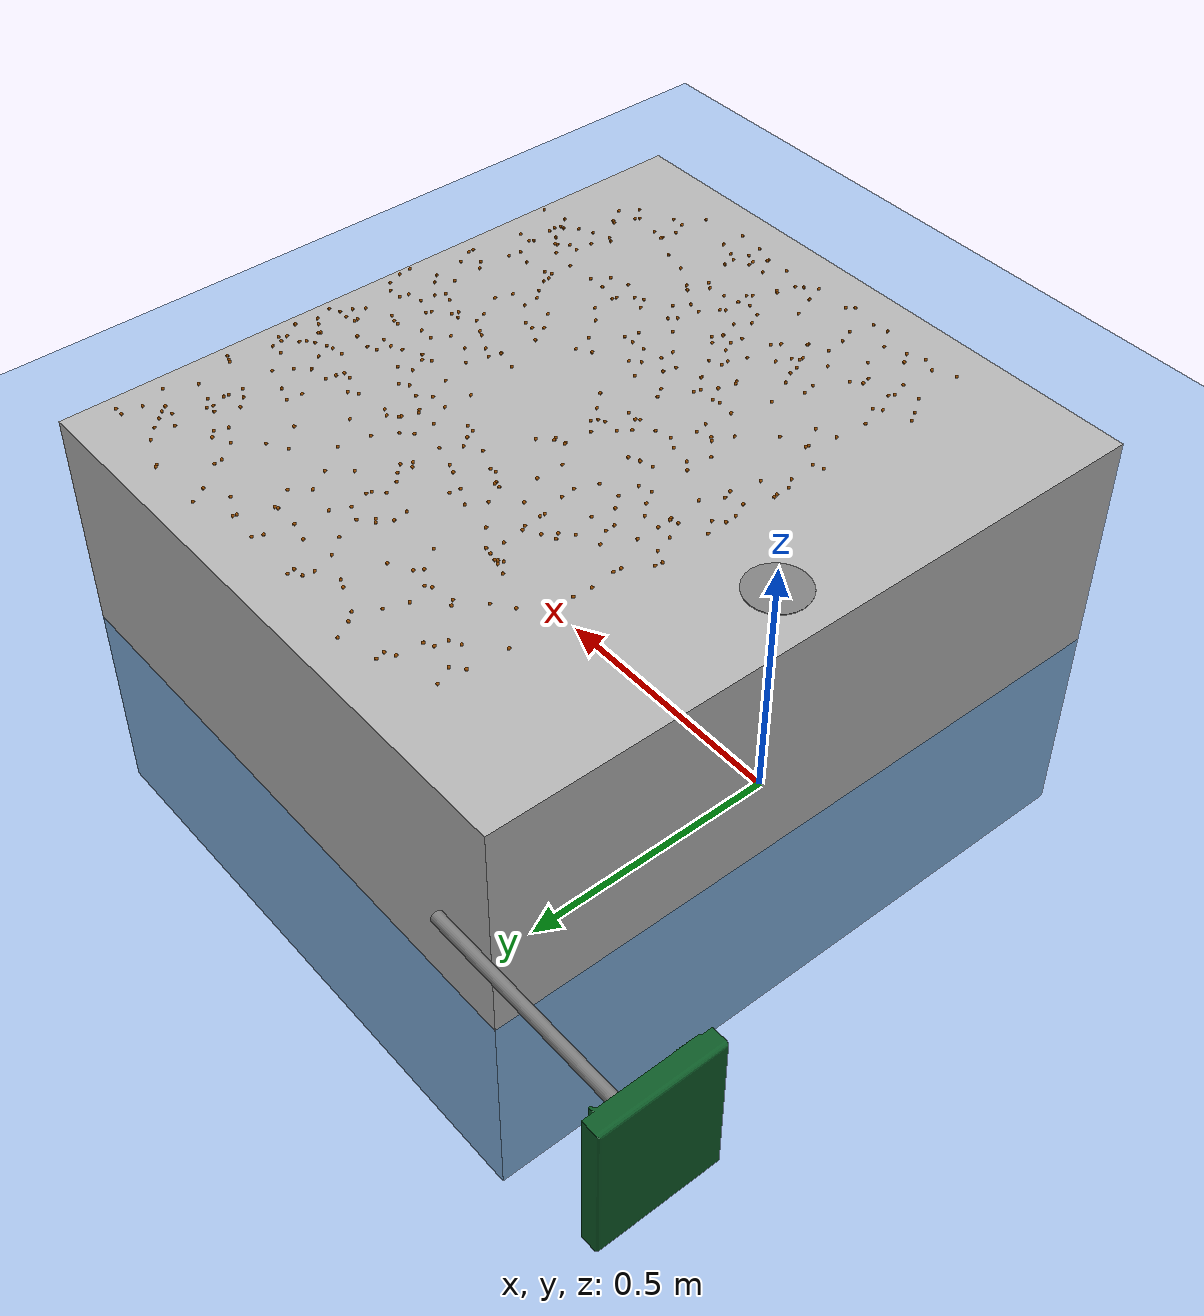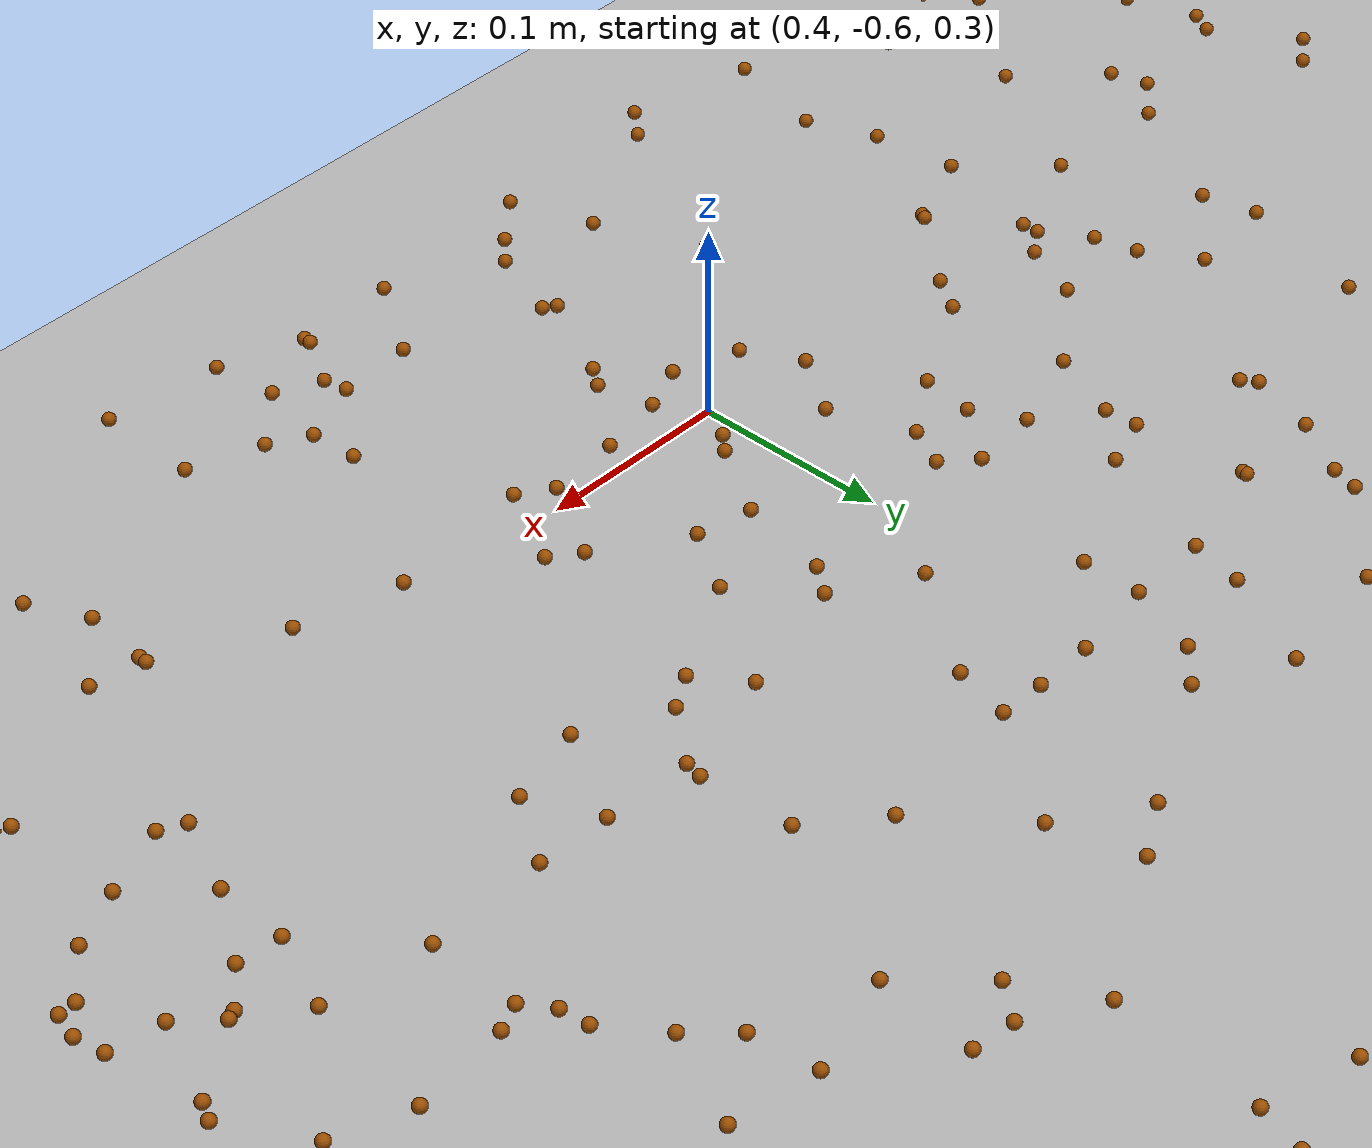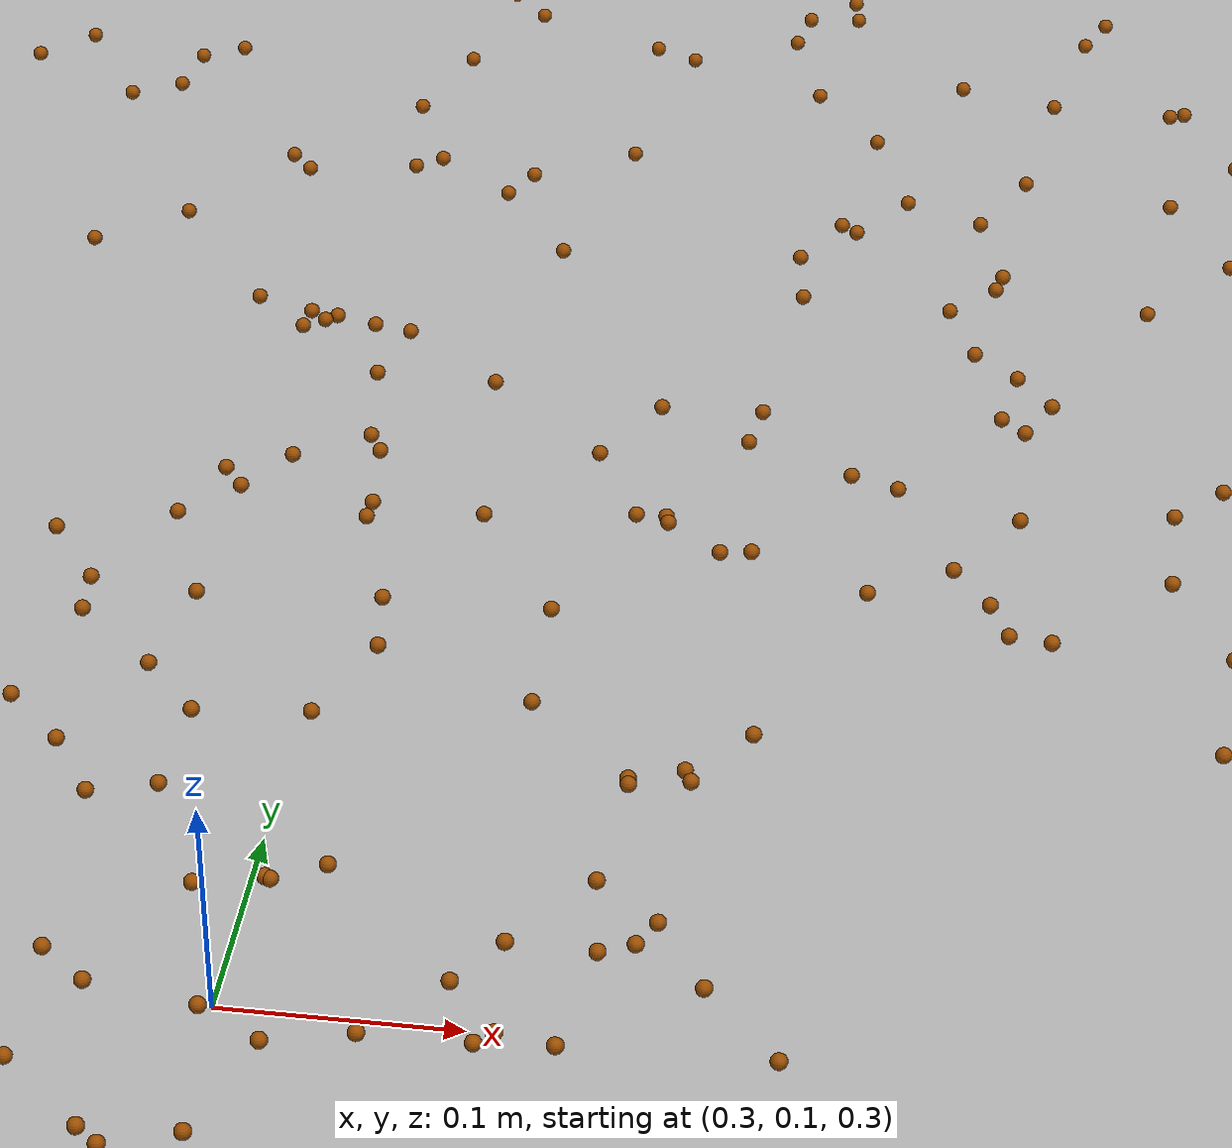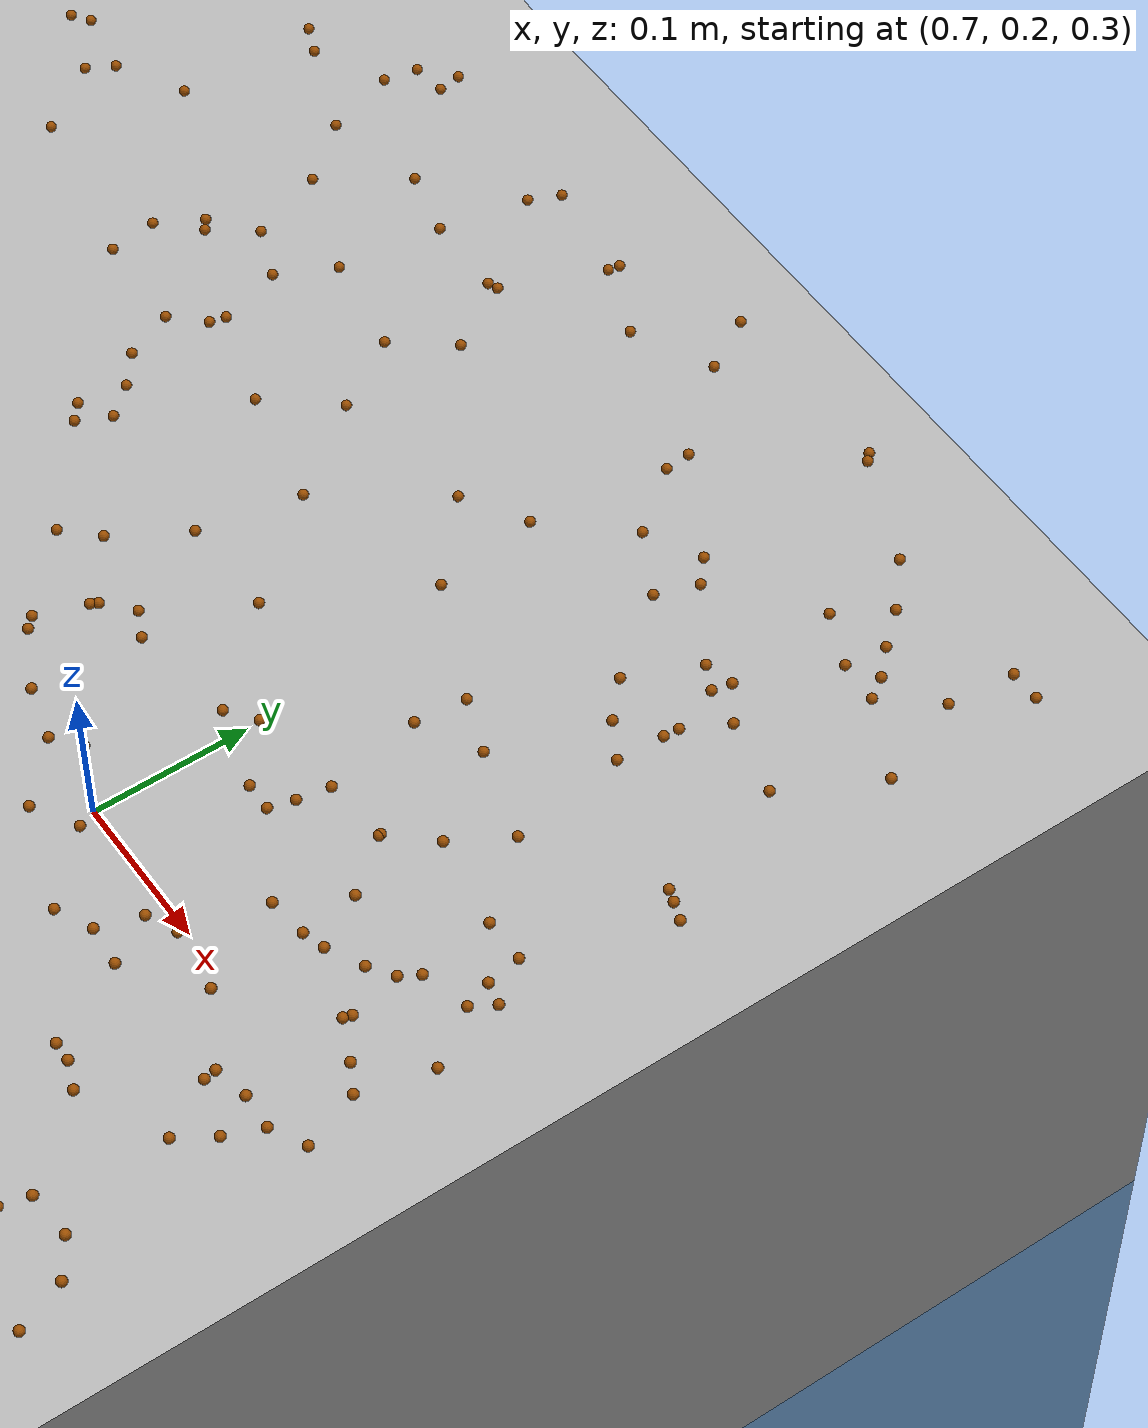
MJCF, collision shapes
<?xml version="1.0" encoding="UTF-8"?>

<mujoco model="ur5e_with_mop_and_dust">
  <compiler angle="radian" meshdir="assets" autolimits="true" />
  <option integrator="implicitfast" timestep="0.01" viscosity="0.01" />

  <!-- ================= DEFAULT SETTINGS ================= -->
  <default>
    <default class="ur5e">
      <default class="visual">
        <geom type="mesh" contype="0" conaffinity="0" group="2" />
      </default>
      <default class="collision">
        <geom type="capsule" group="3" />
        <default class="eef_collision">
          <geom type="cylinder" />
        </default>
      </default>
      <joint axis="0 1 0" range="-6.28319 6.28319" />
      <default class="joint_limited">
        <joint range="-3.1415 3.1415" />
      </default>
      <default class="position">
        <position ctrlrange="-6.2831 6.2831" kp="500" kv="25" forcerange="-150 150" />
        <default class="position_limited">
          <position ctrlrange="-3.1415 3.1415" />
        </default>
        <default class="position_small">
          <position kp="500" kv="25" forcerange="-28 28" />
        </default>
      </default>
    </default>
    <!-- Improved dust particle physics for MuJoCo 3.3.5 -->
    <default class="dust">
      <geom type="sphere" size="0.008" density="600" friction="0.8 0.1 0.05" condim="3"
        contype="1" conaffinity="1" group="1"
        solref="0.02 1.0" solimp="0.9 0.95 0.001" />
    </default>
  </default>

  <!-- ================= VISUAL SETTINGS ================= -->

  <!-- ================= MATERIALS + MESHES ================= -->
  <asset>
    <texture name="skybox" type="skybox" builtin="gradient"
      rgb1="0.7 0.85 1" rgb2="0.2 0.3 0.5" width="512" height="512" />
    <texture name="ground_tex" type="2d" builtin="checker" width="512" height="512"
      rgb1="0.0392 0.5647 0.8588" rgb2="0.9 0.9 1" mark="cross" random="0.01" />
    <material name="ground_mat" texture="ground_tex" texrepeat="10 10"
      rgba="0.0392 0.5647 0.8588 1" specular="0.6" shininess="0.7" reflectance="0.2" />
    <material name="black" rgba="0.033 0.033 0.033 1" />
    <material name="jointgray" rgba="0.278 0.278 0.278 1" />
    <material name="linkgray" rgba="0.82 0.82 0.82 1" />
    <material name="urblue" rgba="0.49 0.678 0.8 1" />
    <material name="table_material" rgba="0.7 0.7 0.7 1" />
    <material name="dust_material" rgba="0.600 0.300 0.0 1" />
    <!-- Purple material for the mop -->
    <material name="mop_purple" rgba="0.18 0.05 0.35 1" specular="0.5" shininess="0.6" />
    <!-- Dark green material for the mop -->
    <material name="mop_dark_green" rgba="0.05 0.35 0.15 1" specular="0.4" shininess="0.5" />

    <!-- Robot meshes -->
    <mesh file="base_0.obj" />
    <mesh file="base_1.obj" />
    <mesh file="shoulder_0.obj" />
    <mesh file="shoulder_1.obj" />
    <mesh file="shoulder_2.obj" />
    <mesh file="upperarm_0.obj" />
    <mesh file="upperarm_1.obj" />
    <mesh file="upperarm_2.obj" />
    <mesh file="upperarm_3.obj" />
    <mesh file="forearm_0.obj" />
    <mesh file="forearm_1.obj" />
    <mesh file="forearm_2.obj" />
    <mesh file="forearm_3.obj" />
    <mesh file="wrist1_0.obj" />
    <mesh file="wrist1_1.obj" />
    <mesh file="wrist1_2.obj" />
    <mesh file="wrist2_0.obj" />
    <mesh file="wrist2_1.obj" />
    <mesh file="wrist2_2.obj" />
    <mesh file="wrist3.obj" />

    <!-- Table and tool meshes -->
    <mesh file="test.stl" scale="1 1.6 1" name="table" />
    <mesh name="base_mesh" file="mop_base.obj" scale="0.002 0.002 0.002" />
    <mesh name="handle_mesh" file="mop_handle.obj" scale="0.0015 0.001 0.0015" />
  </asset>

  <!-- Visual settings: skybox + haze for infinite horizon look -->
  <visual>
    <global offwidth="1280" offheight="720" />
    <map znear="0.01" zfar="200" fogstart="8" fogend="60" />
  </visual>

  <!-- ================= WORLD OBJECTS ================= -->

  <!-- ================= WORLD OBJECTS ================= -->
  <worldbody>
    <!-- Key lights -->
    <!-- Key light (main directional light) -->
    <light name="sun_key" directional="true" pos="2 2 4" dir="-1 -1 -1"
      diffuse="0.3 0.3 0.3" ambient="0.3 0.3 0.35" specular="0.5 0.5 0.5" castshadow="false" />

    <!-- Fill light (soften shadows) -->
    <light name="fill" pos="-2 -2 3" dir="1 1 -1"
      diffuse="0.4 0.4 0.45" ambient="0 0 0" specular="0.2 0.2 0.2" castshadow="false" />

    <!-- Rim/back light (add depth) -->
    <light name="rim" pos="0 3 2.5" dir="0 -1 -1"
      diffuse="0.3 0.35 0.4" ambient="0 0 0" specular="0.15 0.15 0.15" castshadow="false" />

    <!-- Ground with proper contact properties -->
    <geom name="ground" type="plane" size="4 4 0.1" material="ground_mat"
      solref="1.0 1.0" solimp="0.9 0.95 0.001" friction="0.9 0.1 0.05" />
    <!-- Ground with proper contact properties -->
    <!-- pos="-1.35 -0.7 -0.01" -->

    <!-- Table positioned as base platform -->
    <body name="table" pos="0.6 0 0" euler="0 0 1.57079632679">
      <inertial mass="50" pos="0 0 0.05" diaginertia="10 10 5" />
      <geom name="table_collision" type="box" size="0.68 0.6 0.44875" pos="-0.019 0.11 0.01"
        material="table_material" group="3" contype="1" conaffinity="1"
        solref="0.02 1.0" solimp="0.9 0.95 0.001" friction="0.7 0.1 0.05" />
      <geom name="table_visual" type="mesh" mesh="table" material="table_material" class="visual"
        pos="0.65 0.7 -0.142" />
      <!-- 45-deg wedges along table edges (width ≈ 0.10 m, thickness ≈ 0.02 m) -->
      <!-- Table collision box extents in table frame: x in [-2.7, 0], y in [-1.4, 0], top z ≈
        0.49 -->
      <!-- y = 0 edge (north), tilt toward -y -->

      <!-- y = -1.4 edge (south), tilt toward +y -->

      <!-- x = 0 edge (east), tilt toward -x -->

      <!-- x = -2.7 edge (west), tilt toward +x -->
    </body>

    <!-- UR5e Robot mounted ON the table surface -->
    <body name="base" pos="0.0 0.0 0.45" quat="1 0 0 1" childclass="ur5e">
      <inertial mass="4" pos="0 0 0" diaginertia="0.0044 0.0044 0.0072" />
      <geom mesh="base_0" material="black" class="visual" />
      <geom mesh="base_1" material="jointgray" class="visual" />
      <!-- Base collision geometry to sit on table -->
      <geom name="base_collision" type="cylinder" size="0.06 0.02" pos="0 0 -0.01"
        contype="1" conaffinity="1" group="3" friction="0.8 0.1 0.05" />

      <body name="shoulder_link" pos="0 0 0.163">
        <inertial mass="3.7" pos="0 0 0" diaginertia="0.0102 0.0102 0.0066" />
        <joint name="shoulder_pan" axis="0 0 1" />
        <geom mesh="shoulder_0" material="urblue" class="visual" />
        <geom mesh="shoulder_1" material="black" class="visual" />
        <geom mesh="shoulder_2" material="jointgray" class="visual" />

        <body name="upper_arm_link" pos="0 0.138 0" quat="1 0 1 0">
          <inertial mass="8.39" pos="0 0 0.2125" diaginertia="0.133 0.133 0.015" />
          <joint name="shoulder_lift" />
          <geom mesh="upperarm_0" material="linkgray" class="visual" />
          <geom mesh="upperarm_1" material="black" class="visual" />
          <geom mesh="upperarm_2" material="jointgray" class="visual" />
          <geom mesh="upperarm_3" material="urblue" class="visual" />

          <body name="forearm_link" pos="0 -0.131 0.425">
            <inertial mass="2.27" pos="0 0 0.196" diaginertia="0.031 0.031 0.004" />
            <joint name="elbow" class="joint_limited" />
            <geom mesh="forearm_0" material="urblue" class="visual" />
            <geom mesh="forearm_1" material="linkgray" class="visual" />
            <geom mesh="forearm_2" material="black" class="visual" />
            <geom mesh="forearm_3" material="jointgray" class="visual" />

            <body name="wrist_1_link" pos="0 0 0.392" quat="1 0 1 0">
              <inertial mass="1.219" pos="0 0.127 0" diaginertia="0.0025 0.0025 0.0021" />
              <joint name="wrist_1" />
              <geom mesh="wrist1_0" material="black" class="visual" />
              <geom mesh="wrist1_1" material="urblue" class="visual" />
              <geom mesh="wrist1_2" material="jointgray" class="visual" />

              <body name="wrist_2_link" pos="0 0.127 0">
                <inertial mass="1.219" pos="0 0 0.1" diaginertia="0.0025 0.0025 0.0021" />
                <joint name="wrist_2" axis="0 0 1" />
                <geom mesh="wrist2_0" material="black" class="visual" />
                <geom mesh="wrist2_1" material="urblue" class="visual" />
                <geom mesh="wrist2_2" material="jointgray" class="visual" />

                <body name="wrist_3_link" pos="0 0 0.1">
                  <inertial mass="0.188" pos="0 0.077 0" diaginertia="0.00013 0.0001 0.0001" />
                  <joint name="wrist_3" />
                  <geom mesh="wrist3" material="linkgray" class="visual" />

                  <!-- Mop tool attachment -->
                  <body name="mop_mount" pos="0 0.08 0" quat="0 1 0 1">

                    <body name="mop_tool" pos="0 -0.4 0">
                      <inertial mass="0.5" pos="0 0 0" diaginertia="0.01 0.01 0.01" />
                      <geom type="cylinder" size="0.01 0.2" pos="0 0.2 0"
                        euler="1.57079632679 0 0" group="1" contype="1" conaffinity="1"
                        solref="0.02 1.0" solimp="0.9 0.95 0.001" friction="0.8 0.1 0.05" />

                      <body name="mop_head">
                        <joint name="mop_socket" type="ball" damping="0.5" limited="false" />
                        <site name="ee_site" pos="0 -0.02 0.0" size="0.01" rgba="1 0 0 1" group="4" />
                        <inertial mass="0.2" pos="0 -0.05 -0.1" diaginertia="0.005 0.005 0.005" />
                        <geom type="mesh" mesh="base_mesh" density="500" friction="0.8 0.1 0.1"
                          pos="0 -0.05 -0.1" material="mop_dark_green" />
                        <geom name="mop_pad" type="box" size="0.12 0.005 0.09"
                          pos="0 -0.04 0.0"
                          euler="0 0 0"
                          contype="1" conaffinity="1"
                          solref="0.006 1.0" solimp="0.85 0.8 0.0005"
                          friction="0.01 0.01 0.05"
                          rgba="0.2 0.6 0.2 0.3" group="3" />
                      </body>  <!--
                      mop_head -->
                    </body>    <!--
                    mop_tool -->
                  </body>      <!--
                  mop_mount -->
                </body>        <!--
                wrist_3_link -->
              </body>          <!--
              wrist_2_link -->
            </body>            <!--
            wrist_1_link -->
          </body>              <!--
          forearm_link -->
        </body>                <!--
        upper_arm_link -->
      </body>                  <!--
      shoulder_link -->
    </body>                    <!--
    base -->

    <!-- Dust particles properly positioned on table surface around the robot -->
    <!-- Distributed in a cleaning area away from robot base -->
    <!-- Dust balls (stable with solver parameters) -->

    <!-- Dust particles - stable until mop pushes them -->

     <body name="ball_1" pos="0.5705 -0.5347 0.48">
      <freejoint/>
      <inertial mass="0.0025" diaginertia="9.000000000000001e-09 9.000000000000001e-09 9.000000000000001e-09" pos="0 0 0"/>
      <geom type="sphere" size="0.003" material="dust_material"/>
   </body>
   <body name="ball_2" pos="0.5891 -0.2293 0.48">
      <freejoint/>
      <inertial mass="0.0025" diaginertia="9.000000000000001e-09 9.000000000000001e-09 9.000000000000001e-09" pos="0 0 0"/>
      <geom type="sphere" size="0.003" material="dust_material"/>
   </body>
   <body name="ball_3" pos="0.3441 0.2361 0.48">
      <freejoint/>
      <inertial mass="0.0025" diaginertia="9.000000000000001e-09 9.000000000000001e-09 9.000000000000001e-09" pos="0 0 0"/>
      <geom type="sphere" size="0.003" material="dust_material"/>
   </body>
   <body name="ball_4" pos="0.5399 -0.167 0.48">
      <freejoint/>
      <inertial mass="0.0025" diaginertia="9.000000000000001e-09 9.000000000000001e-09 9.000000000000001e-09" pos="0 0 0"/>
      <geom type="sphere" size="0.003" material="dust_material"/>
   </body>
   <body name="ball_5" pos="0.7121 -0.5505 0.48">
      <freejoint/>
      <inertial mass="0.0025" diaginertia="9.000000000000001e-09 9.000000000000001e-09 9.000000000000001e-09" pos="0 0 0"/>
      <geom type="sphere" size="0.003" material="dust_material"/>
   </body>
   <body name="ball_6" pos="0.7957 -0.3264 0.48">
      <freejoint/>
      <inertial mass="0.0025" diaginertia="9.000000000000001e-09 9.000000000000001e-09 9.000000000000001e-09" pos="0 0 0"/>
      <geom type="sphere" size="0.003" material="dust_material"/>
   </body>
   <body name="ball_7" pos="0.7798 -0.1648 0.48">
      <freejoint/>
      <inertial mass="0.0025" diaginertia="9.000000000000001e-09 9.000000000000001e-09 9.000000000000001e-09" pos="0 0 0"/>
      <geom type="sphere" size="0.003" material="dust_material"/>
   </body>
   <body name="ball_8" pos="0.1434 0.1141 0.48">
      <freejoint/>
      <inertial mass="0.0025" diaginertia="9.000000000000001e-09 9.000000000000001e-09 9.000000000000001e-09" pos="0 0 0"/>
      <geom type="sphere" size="0.003" material="dust_material"/>
   </body>
   <body name="ball_9" pos="0.2189 -0.4668 0.48">
      <freejoint/>
      <inertial mass="0.0025" diaginertia="9.000000000000001e-09 9.000000000000001e-09 9.000000000000001e-09" pos="0 0 0"/>
      <geom type="sphere" size="0.003" material="dust_material"/>
   </body>
   <body name="ball_10" pos="0.198 0.0328 0.48">
      <freejoint/>
      <inertial mass="0.0025" diaginertia="9.000000000000001e-09 9.000000000000001e-09 9.000000000000001e-09" pos="0 0 0"/>
      <geom type="sphere" size="0.003" material="dust_material"/>
   </body>
   <body name="ball_11" pos="0.6544 0.1837 0.48">
      <freejoint/>
      <inertial mass="0.0025" diaginertia="9.000000000000001e-09 9.000000000000001e-09 9.000000000000001e-09" pos="0 0 0"/>
      <geom type="sphere" size="0.003" material="dust_material"/>
   </body>
   <body name="ball_12" pos="0.3901 -0.4206 0.48">
      <freejoint/>
      <inertial mass="0.0025" diaginertia="9.000000000000001e-09 9.000000000000001e-09 9.000000000000001e-09" pos="0 0 0"/>
      <geom type="sphere" size="0.003" material="dust_material"/>
   </body>
   <body name="ball_13" pos="1.0306 0.2493 0.48">
      <freejoint/>
      <inertial mass="0.0025" diaginertia="9.000000000000001e-09 9.000000000000001e-09 9.000000000000001e-09" pos="0 0 0"/>
      <geom type="sphere" size="0.003" material="dust_material"/>
   </body>
   <body name="ball_14" pos="0.4331 0.2362 0.48">
      <freejoint/>
      <inertial mass="0.0025" diaginertia="9.000000000000001e-09 9.000000000000001e-09 9.000000000000001e-09" pos="0 0 0"/>
      <geom type="sphere" size="0.003" material="dust_material"/>
   </body>
   <body name="ball_15" pos="0.9791 -0.3633 0.48">
      <freejoint/>
      <inertial mass="0.0025" diaginertia="9.000000000000001e-09 9.000000000000001e-09 9.000000000000001e-09" pos="0 0 0"/>
      <geom type="sphere" size="0.003" material="dust_material"/>
   </body>
   <body name="ball_16" pos="0.9463 0.5543 0.48">
      <freejoint/>
      <inertial mass="0.0025" diaginertia="9.000000000000001e-09 9.000000000000001e-09 9.000000000000001e-09" pos="0 0 0"/>
      <geom type="sphere" size="0.003" material="dust_material"/>
   </body>
   <body name="ball_17" pos="0.2134 -0.477 0.48">
      <freejoint/>
      <inertial mass="0.0025" diaginertia="9.000000000000001e-09 9.000000000000001e-09 9.000000000000001e-09" pos="0 0 0"/>
      <geom type="sphere" size="0.003" material="dust_material"/>
   </body>
   <body name="ball_18" pos="0.3956 0.1917 0.48">
      <freejoint/>
      <inertial mass="0.0025" diaginertia="9.000000000000001e-09 9.000000000000001e-09 9.000000000000001e-09" pos="0 0 0"/>
      <geom type="sphere" size="0.003" material="dust_material"/>
   </body>
   <body name="ball_19" pos="0.2674 0.041 0.48">
      <freejoint/>
      <inertial mass="0.0025" diaginertia="9.000000000000001e-09 9.000000000000001e-09 9.000000000000001e-09" pos="0 0 0"/>
      <geom type="sphere" size="0.003" material="dust_material"/>
   </body>
   <body name="ball_20" pos="0.9843 0.117 0.48">
      <freejoint/>
      <inertial mass="0.0025" diaginertia="9.000000000000001e-09 9.000000000000001e-09 9.000000000000001e-09" pos="0 0 0"/>
      <geom type="sphere" size="0.003" material="dust_material"/>
   </body>
   <body name="ball_21" pos="0.5869 -0.49 0.48">
      <freejoint/>
      <inertial mass="0.0025" diaginertia="9.000000000000001e-09 9.000000000000001e-09 9.000000000000001e-09" pos="0 0 0"/>
      <geom type="sphere" size="0.003" material="dust_material"/>
   </body>
   <body name="ball_22" pos="0.4421 -0.0434 0.48">
      <freejoint/>
      <inertial mass="0.0025" diaginertia="9.000000000000001e-09 9.000000000000001e-09 9.000000000000001e-09" pos="0 0 0"/>
      <geom type="sphere" size="0.003" material="dust_material"/>
   </body>
   <body name="ball_23" pos="0.7394 -0.0272 0.48">
      <freejoint/>
      <inertial mass="0.0025" diaginertia="9.000000000000001e-09 9.000000000000001e-09 9.000000000000001e-09" pos="0 0 0"/>
      <geom type="sphere" size="0.003" material="dust_material"/>
   </body>
   <body name="ball_24" pos="0.9137 0.2565 0.48">
      <freejoint/>
      <inertial mass="0.0025" diaginertia="9.000000000000001e-09 9.000000000000001e-09 9.000000000000001e-09" pos="0 0 0"/>
      <geom type="sphere" size="0.003" material="dust_material"/>
   </body>
   <body name="ball_25" pos="0.9885 0.2723 0.48">
      <freejoint/>
      <inertial mass="0.0025" diaginertia="9.000000000000001e-09 9.000000000000001e-09 9.000000000000001e-09" pos="0 0 0"/>
      <geom type="sphere" size="0.003" material="dust_material"/>
   </body>
   <body name="ball_26" pos="0.9942 0.0097 0.48">
      <freejoint/>
      <inertial mass="0.0025" diaginertia="9.000000000000001e-09 9.000000000000001e-09 9.000000000000001e-09" pos="0 0 0"/>
      <geom type="sphere" size="0.003" material="dust_material"/>
   </body>
   <body name="ball_27" pos="0.3549 -0.2248 0.48">
      <freejoint/>
      <inertial mass="0.0025" diaginertia="9.000000000000001e-09 9.000000000000001e-09 9.000000000000001e-09" pos="0 0 0"/>
      <geom type="sphere" size="0.003" material="dust_material"/>
   </body>
   <body name="ball_28" pos="0.8045 -0.033 0.48">
      <freejoint/>
      <inertial mass="0.0025" diaginertia="9.000000000000001e-09 9.000000000000001e-09 9.000000000000001e-09" pos="0 0 0"/>
      <geom type="sphere" size="0.003" material="dust_material"/>
   </body>
   <body name="ball_29" pos="0.53 -0.3658 0.48">
      <freejoint/>
      <inertial mass="0.0025" diaginertia="9.000000000000001e-09 9.000000000000001e-09 9.000000000000001e-09" pos="0 0 0"/>
      <geom type="sphere" size="0.003" material="dust_material"/>
   </body>
   <body name="ball_30" pos="0.153 0.5456 0.48">
      <freejoint/>
      <inertial mass="0.0025" diaginertia="9.000000000000001e-09 9.000000000000001e-09 9.000000000000001e-09" pos="0 0 0"/>
      <geom type="sphere" size="0.003" material="dust_material"/>
   </body>
   <body name="ball_31" pos="0.3166 -0.3618 0.48">
      <freejoint/>
      <inertial mass="0.0025" diaginertia="9.000000000000001e-09 9.000000000000001e-09 9.000000000000001e-09" pos="0 0 0"/>
      <geom type="sphere" size="0.003" material="dust_material"/>
   </body>
   <body name="ball_32" pos="0.3376 0.4346 0.48">
      <freejoint/>
      <inertial mass="0.0025" diaginertia="9.000000000000001e-09 9.000000000000001e-09 9.000000000000001e-09" pos="0 0 0"/>
      <geom type="sphere" size="0.003" material="dust_material"/>
   </body>
   <body name="ball_33" pos="0.9287 0.5245 0.48">
      <freejoint/>
      <inertial mass="0.0025" diaginertia="9.000000000000001e-09 9.000000000000001e-09 9.000000000000001e-09" pos="0 0 0"/>
      <geom type="sphere" size="0.003" material="dust_material"/>
   </body>
   <body name="ball_34" pos="0.4741 0.5472 0.48">
      <freejoint/>
      <inertial mass="0.0025" diaginertia="9.000000000000001e-09 9.000000000000001e-09 9.000000000000001e-09" pos="0 0 0"/>
      <geom type="sphere" size="0.003" material="dust_material"/>
   </body>
   <body name="ball_35" pos="0.4023 -0.4118 0.48">
      <freejoint/>
      <inertial mass="0.0025" diaginertia="9.000000000000001e-09 9.000000000000001e-09 9.000000000000001e-09" pos="0 0 0"/>
      <geom type="sphere" size="0.003" material="dust_material"/>
   </body>
   <body name="ball_36" pos="0.8322 -0.5188 0.48">
      <freejoint/>
      <inertial mass="0.0025" diaginertia="9.000000000000001e-09 9.000000000000001e-09 9.000000000000001e-09" pos="0 0 0"/>
      <geom type="sphere" size="0.003" material="dust_material"/>
   </body>
   <body name="ball_37" pos="0.6298 -0.5559 0.48">
      <freejoint/>
      <inertial mass="0.0025" diaginertia="9.000000000000001e-09 9.000000000000001e-09 9.000000000000001e-09" pos="0 0 0"/>
      <geom type="sphere" size="0.003" material="dust_material"/>
   </body>
   <body name="ball_38" pos="1.0224 0.3561 0.48">
      <freejoint/>
      <inertial mass="0.0025" diaginertia="9.000000000000001e-09 9.000000000000001e-09 9.000000000000001e-09" pos="0 0 0"/>
      <geom type="sphere" size="0.003" material="dust_material"/>
   </body>
   <body name="ball_39" pos="0.8877 -0.4045 0.48">
      <freejoint/>
      <inertial mass="0.0025" diaginertia="9.000000000000001e-09 9.000000000000001e-09 9.000000000000001e-09" pos="0 0 0"/>
      <geom type="sphere" size="0.003" material="dust_material"/>
   </body>
   <body name="ball_40" pos="1.0254 0.1201 0.48">
      <freejoint/>
      <inertial mass="0.0025" diaginertia="9.000000000000001e-09 9.000000000000001e-09 9.000000000000001e-09" pos="0 0 0"/>
      <geom type="sphere" size="0.003" material="dust_material"/>
   </body>
   <body name="ball_41" pos="0.2985 0.1308 0.48">
      <freejoint/>
      <inertial mass="0.0025" diaginertia="9.000000000000001e-09 9.000000000000001e-09 9.000000000000001e-09" pos="0 0 0"/>
      <geom type="sphere" size="0.003" material="dust_material"/>
   </body>
   <body name="ball_42" pos="0.2709 -0.4583 0.48">
      <freejoint/>
      <inertial mass="0.0025" diaginertia="9.000000000000001e-09 9.000000000000001e-09 9.000000000000001e-09" pos="0 0 0"/>
      <geom type="sphere" size="0.003" material="dust_material"/>
   </body>
   <body name="ball_43" pos="0.3036 0.3056 0.48">
      <freejoint/>
      <inertial mass="0.0025" diaginertia="9.000000000000001e-09 9.000000000000001e-09 9.000000000000001e-09" pos="0 0 0"/>
      <geom type="sphere" size="0.003" material="dust_material"/>
   </body>
   <body name="ball_44" pos="0.8442 -0.5448 0.48">
      <freejoint/>
      <inertial mass="0.0025" diaginertia="9.000000000000001e-09 9.000000000000001e-09 9.000000000000001e-09" pos="0 0 0"/>
      <geom type="sphere" size="0.003" material="dust_material"/>
   </body>
   <body name="ball_45" pos="0.2074 -0.2654 0.48">
      <freejoint/>
      <inertial mass="0.0025" diaginertia="9.000000000000001e-09 9.000000000000001e-09 9.000000000000001e-09" pos="0 0 0"/>
      <geom type="sphere" size="0.003" material="dust_material"/>
   </body>
   <body name="ball_46" pos="0.9914 -0.3509 0.48">
      <freejoint/>
      <inertial mass="0.0025" diaginertia="9.000000000000001e-09 9.000000000000001e-09 9.000000000000001e-09" pos="0 0 0"/>
      <geom type="sphere" size="0.003" material="dust_material"/>
   </body>
   <body name="ball_47" pos="0.4736 -0.0442 0.48">
      <freejoint/>
      <inertial mass="0.0025" diaginertia="9.000000000000001e-09 9.000000000000001e-09 9.000000000000001e-09" pos="0 0 0"/>
      <geom type="sphere" size="0.003" material="dust_material"/>
   </body>
   <body name="ball_48" pos="0.9014 0.4115 0.48">
      <freejoint/>
      <inertial mass="0.0025" diaginertia="9.000000000000001e-09 9.000000000000001e-09 9.000000000000001e-09" pos="0 0 0"/>
      <geom type="sphere" size="0.003" material="dust_material"/>
   </body>
   <body name="ball_49" pos="0.6764 -0.176 0.48">
      <freejoint/>
      <inertial mass="0.0025" diaginertia="9.000000000000001e-09 9.000000000000001e-09 9.000000000000001e-09" pos="0 0 0"/>
      <geom type="sphere" size="0.003" material="dust_material"/>
   </body>
   <body name="ball_50" pos="0.398 0.3724 0.48">
      <freejoint/>
      <inertial mass="0.0025" diaginertia="9.000000000000001e-09 9.000000000000001e-09 9.000000000000001e-09" pos="0 0 0"/>
      <geom type="sphere" size="0.003" material="dust_material"/>
   </body>
   <body name="ball_51" pos="0.7899 0.432 0.48">
      <freejoint/>
      <inertial mass="0.0025" diaginertia="9.000000000000001e-09 9.000000000000001e-09 9.000000000000001e-09" pos="0 0 0"/>
      <geom type="sphere" size="0.003" material="dust_material"/>
   </body>
   <body name="ball_52" pos="0.7364 -0.4472 0.48">
      <freejoint/>
      <inertial mass="0.0025" diaginertia="9.000000000000001e-09 9.000000000000001e-09 9.000000000000001e-09" pos="0 0 0"/>
      <geom type="sphere" size="0.003" material="dust_material"/>
   </body>
   <body name="ball_53" pos="1.0407 0.3499 0.48">
      <freejoint/>
      <inertial mass="0.0025" diaginertia="9.000000000000001e-09 9.000000000000001e-09 9.000000000000001e-09" pos="0 0 0"/>
      <geom type="sphere" size="0.003" material="dust_material"/>
   </body>
   <body name="ball_54" pos="0.4167 0.449 0.48">
      <freejoint/>
      <inertial mass="0.0025" diaginertia="9.000000000000001e-09 9.000000000000001e-09 9.000000000000001e-09" pos="0 0 0"/>
      <geom type="sphere" size="0.003" material="dust_material"/>
   </body>
   <body name="ball_55" pos="0.4108 -0.2864 0.48">
      <freejoint/>
      <inertial mass="0.0025" diaginertia="9.000000000000001e-09 9.000000000000001e-09 9.000000000000001e-09" pos="0 0 0"/>
      <geom type="sphere" size="0.003" material="dust_material"/>
   </body>
   <body name="ball_56" pos="0.4145 -0.4621 0.48">
      <freejoint/>
      <inertial mass="0.0025" diaginertia="9.000000000000001e-09 9.000000000000001e-09 9.000000000000001e-09" pos="0 0 0"/>
      <geom type="sphere" size="0.003" material="dust_material"/>
   </body>
   <body name="ball_57" pos="0.8845 0.0409 0.48">
      <freejoint/>
      <inertial mass="0.0025" diaginertia="9.000000000000001e-09 9.000000000000001e-09 9.000000000000001e-09" pos="0 0 0"/>
      <geom type="sphere" size="0.003" material="dust_material"/>
   </body>
   <body name="ball_58" pos="0.4984 0.3524 0.48">
      <freejoint/>
      <inertial mass="0.0025" diaginertia="9.000000000000001e-09 9.000000000000001e-09 9.000000000000001e-09" pos="0 0 0"/>
      <geom type="sphere" size="0.003" material="dust_material"/>
   </body>
   <body name="ball_59" pos="0.5665 -0.4648 0.48">
      <freejoint/>
      <inertial mass="0.0025" diaginertia="9.000000000000001e-09 9.000000000000001e-09 9.000000000000001e-09" pos="0 0 0"/>
      <geom type="sphere" size="0.003" material="dust_material"/>
   </body>
   <body name="ball_60" pos="0.1501 0.4943 0.48">
      <freejoint/>
      <inertial mass="0.0025" diaginertia="9.000000000000001e-09 9.000000000000001e-09 9.000000000000001e-09" pos="0 0 0"/>
      <geom type="sphere" size="0.003" material="dust_material"/>
   </body>
   <body name="ball_61" pos="0.6672 0.3965 0.48">
      <freejoint/>
      <inertial mass="0.0025" diaginertia="9.000000000000001e-09 9.000000000000001e-09 9.000000000000001e-09" pos="0 0 0"/>
      <geom type="sphere" size="0.003" material="dust_material"/>
   </body>
   <body name="ball_62" pos="0.4394 -0.6069 0.48">
      <freejoint/>
      <inertial mass="0.0025" diaginertia="9.000000000000001e-09 9.000000000000001e-09 9.000000000000001e-09" pos="0 0 0"/>
      <geom type="sphere" size="0.003" material="dust_material"/>
   </body>
   <body name="ball_63" pos="0.8753 -0.2501 0.48">
      <freejoint/>
      <inertial mass="0.0025" diaginertia="9.000000000000001e-09 9.000000000000001e-09 9.000000000000001e-09" pos="0 0 0"/>
      <geom type="sphere" size="0.003" material="dust_material"/>
   </body>
   <body name="ball_64" pos="0.3466 -0.0877 0.48">
      <freejoint/>
      <inertial mass="0.0025" diaginertia="9.000000000000001e-09 9.000000000000001e-09 9.000000000000001e-09" pos="0 0 0"/>
      <geom type="sphere" size="0.003" material="dust_material"/>
   </body>
   <body name="ball_65" pos="0.3334 -0.3001 0.48">
      <freejoint/>
      <inertial mass="0.0025" diaginertia="9.000000000000001e-09 9.000000000000001e-09 9.000000000000001e-09" pos="0 0 0"/>
      <geom type="sphere" size="0.003" material="dust_material"/>
   </body>
   <body name="ball_66" pos="0.1889 -0.3813 0.48">
      <freejoint/>
      <inertial mass="0.0025" diaginertia="9.000000000000001e-09 9.000000000000001e-09 9.000000000000001e-09" pos="0 0 0"/>
      <geom type="sphere" size="0.003" material="dust_material"/>
   </body>
   <body name="ball_67" pos="0.8799 -0.122 0.48">
      <freejoint/>
      <inertial mass="0.0025" diaginertia="9.000000000000001e-09 9.000000000000001e-09 9.000000000000001e-09" pos="0 0 0"/>
      <geom type="sphere" size="0.003" material="dust_material"/>
   </body>
   <body name="ball_68" pos="0.4009 -0.0938 0.48">
      <freejoint/>
      <inertial mass="0.0025" diaginertia="9.000000000000001e-09 9.000000000000001e-09 9.000000000000001e-09" pos="0 0 0"/>
      <geom type="sphere" size="0.003" material="dust_material"/>
   </body>
   <body name="ball_69" pos="0.5699 0.3214 0.48">
      <freejoint/>
      <inertial mass="0.0025" diaginertia="9.000000000000001e-09 9.000000000000001e-09 9.000000000000001e-09" pos="0 0 0"/>
      <geom type="sphere" size="0.003" material="dust_material"/>
   </body>
   <body name="ball_70" pos="0.4779 0.5672 0.48">
      <freejoint/>
      <inertial mass="0.0025" diaginertia="9.000000000000001e-09 9.000000000000001e-09 9.000000000000001e-09" pos="0 0 0"/>
      <geom type="sphere" size="0.003" material="dust_material"/>
   </body>
   <body name="ball_71" pos="0.8577 0.6027 0.48">
      <freejoint/>
      <inertial mass="0.0025" diaginertia="9.000000000000001e-09 9.000000000000001e-09 9.000000000000001e-09" pos="0 0 0"/>
      <geom type="sphere" size="0.003" material="dust_material"/>
   </body>
   <body name="ball_72" pos="0.2407 0.3809 0.48">
      <freejoint/>
      <inertial mass="0.0025" diaginertia="9.000000000000001e-09 9.000000000000001e-09 9.000000000000001e-09" pos="0 0 0"/>
      <geom type="sphere" size="0.003" material="dust_material"/>
   </body>
   <body name="ball_73" pos="0.9721 -0.2258 0.48">
      <freejoint/>
      <inertial mass="0.0025" diaginertia="9.000000000000001e-09 9.000000000000001e-09 9.000000000000001e-09" pos="0 0 0"/>
      <geom type="sphere" size="0.003" material="dust_material"/>
   </body>
   <body name="ball_74" pos="0.9134 -0.4974 0.48">
      <freejoint/>
      <inertial mass="0.0025" diaginertia="9.000000000000001e-09 9.000000000000001e-09 9.000000000000001e-09" pos="0 0 0"/>
      <geom type="sphere" size="0.003" material="dust_material"/>
   </body>
   <body name="ball_75" pos="0.6865 -0.5734 0.48">
      <freejoint/>
      <inertial mass="0.0025" diaginertia="9.000000000000001e-09 9.000000000000001e-09 9.000000000000001e-09" pos="0 0 0"/>
      <geom type="sphere" size="0.003" material="dust_material"/>
   </body>
   <body name="ball_76" pos="0.4134 -0.4643 0.48">
      <freejoint/>
      <inertial mass="0.0025" diaginertia="9.000000000000001e-09 9.000000000000001e-09 9.000000000000001e-09" pos="0 0 0"/>
      <geom type="sphere" size="0.003" material="dust_material"/>
   </body>
   <body name="ball_77" pos="0.5736 0.181 0.48">
      <freejoint/>
      <inertial mass="0.0025" diaginertia="9.000000000000001e-09 9.000000000000001e-09 9.000000000000001e-09" pos="0 0 0"/>
      <geom type="sphere" size="0.003" material="dust_material"/>
   </body>
   <body name="ball_78" pos="0.1449 0.4184 0.48">
      <freejoint/>
      <inertial mass="0.0025" diaginertia="9.000000000000001e-09 9.000000000000001e-09 9.000000000000001e-09" pos="0 0 0"/>
      <geom type="sphere" size="0.003" material="dust_material"/>
   </body>
   <body name="ball_79" pos="0.5838 -0.4212 0.48">
      <freejoint/>
      <inertial mass="0.0025" diaginertia="9.000000000000001e-09 9.000000000000001e-09 9.000000000000001e-09" pos="0 0 0"/>
      <geom type="sphere" size="0.003" material="dust_material"/>
   </body>
   <body name="ball_80" pos="0.6121 -0.38 0.48">
      <freejoint/>
      <inertial mass="0.0025" diaginertia="9.000000000000001e-09 9.000000000000001e-09 9.000000000000001e-09" pos="0 0 0"/>
      <geom type="sphere" size="0.003" material="dust_material"/>
   </body>
   <body name="ball_81" pos="0.9644 -0.333 0.48">
      <freejoint/>
      <inertial mass="0.0025" diaginertia="9.000000000000001e-09 9.000000000000001e-09 9.000000000000001e-09" pos="0 0 0"/>
      <geom type="sphere" size="0.003" material="dust_material"/>
   </body>
   <body name="ball_82" pos="0.9888 0.2178 0.48">
      <freejoint/>
      <inertial mass="0.0025" diaginertia="9.000000000000001e-09 9.000000000000001e-09 9.000000000000001e-09" pos="0 0 0"/>
      <geom type="sphere" size="0.003" material="dust_material"/>
   </body>
   <body name="ball_83" pos="0.2112 0.0641 0.48">
      <freejoint/>
      <inertial mass="0.0025" diaginertia="9.000000000000001e-09 9.000000000000001e-09 9.000000000000001e-09" pos="0 0 0"/>
      <geom type="sphere" size="0.003" material="dust_material"/>
   </body>
   <body name="ball_84" pos="0.1757 0.1878 0.48">
      <freejoint/>
      <inertial mass="0.0025" diaginertia="9.000000000000001e-09 9.000000000000001e-09 9.000000000000001e-09" pos="0 0 0"/>
      <geom type="sphere" size="0.003" material="dust_material"/>
   </body>
   <body name="ball_85" pos="0.7549 0.286 0.48">
      <freejoint/>
      <inertial mass="0.0025" diaginertia="9.000000000000001e-09 9.000000000000001e-09 9.000000000000001e-09" pos="0 0 0"/>
      <geom type="sphere" size="0.003" material="dust_material"/>
   </body>
   <body name="ball_86" pos="0.799 0.1225 0.48">
      <freejoint/>
      <inertial mass="0.0025" diaginertia="9.000000000000001e-09 9.000000000000001e-09 9.000000000000001e-09" pos="0 0 0"/>
      <geom type="sphere" size="0.003" material="dust_material"/>
   </body>
   <body name="ball_87" pos="0.7449 -0.5616 0.48">
      <freejoint/>
      <inertial mass="0.0025" diaginertia="9.000000000000001e-09 9.000000000000001e-09 9.000000000000001e-09" pos="0 0 0"/>
      <geom type="sphere" size="0.003" material="dust_material"/>
   </body>
   <body name="ball_88" pos="0.7013 0.1792 0.48">
      <freejoint/>
      <inertial mass="0.0025" diaginertia="9.000000000000001e-09 9.000000000000001e-09 9.000000000000001e-09" pos="0 0 0"/>
      <geom type="sphere" size="0.003" material="dust_material"/>
   </body>
   <body name="ball_89" pos="0.3772 -0.4002 0.48">
      <freejoint/>
      <inertial mass="0.0025" diaginertia="9.000000000000001e-09 9.000000000000001e-09 9.000000000000001e-09" pos="0 0 0"/>
      <geom type="sphere" size="0.003" material="dust_material"/>
   </body>
   <body name="ball_90" pos="0.6173 -0.2277 0.48">
      <freejoint/>
      <inertial mass="0.0025" diaginertia="9.000000000000001e-09 9.000000000000001e-09 9.000000000000001e-09" pos="0 0 0"/>
      <geom type="sphere" size="0.003" material="dust_material"/>
   </body>
   <body name="ball_91" pos="0.5117 0.0761 0.48">
      <freejoint/>
      <inertial mass="0.0025" diaginertia="9.000000000000001e-09 9.000000000000001e-09 9.000000000000001e-09" pos="0 0 0"/>
      <geom type="sphere" size="0.003" material="dust_material"/>
   </body>
   <body name="ball_92" pos="0.6898 -0.6026 0.48">
      <freejoint/>
      <inertial mass="0.0025" diaginertia="9.000000000000001e-09 9.000000000000001e-09 9.000000000000001e-09" pos="0 0 0"/>
      <geom type="sphere" size="0.003" material="dust_material"/>
   </body>
   <body name="ball_93" pos="0.5882 -0.4556 0.48">
      <freejoint/>
      <inertial mass="0.0025" diaginertia="9.000000000000001e-09 9.000000000000001e-09 9.000000000000001e-09" pos="0 0 0"/>
      <geom type="sphere" size="0.003" material="dust_material"/>
   </body>
   <body name="ball_94" pos="0.2317 -0.3057 0.48">
      <freejoint/>
      <inertial mass="0.0025" diaginertia="9.000000000000001e-09 9.000000000000001e-09 9.000000000000001e-09" pos="0 0 0"/>
      <geom type="sphere" size="0.003" material="dust_material"/>
   </body>
   <body name="ball_95" pos="0.8911 -0.0312 0.48">
      <freejoint/>
      <inertial mass="0.0025" diaginertia="9.000000000000001e-09 9.000000000000001e-09 9.000000000000001e-09" pos="0 0 0"/>
      <geom type="sphere" size="0.003" material="dust_material"/>
   </body>
   <body name="ball_96" pos="0.415 -0.2929 0.48">
      <freejoint/>
      <inertial mass="0.0025" diaginertia="9.000000000000001e-09 9.000000000000001e-09 9.000000000000001e-09" pos="0 0 0"/>
      <geom type="sphere" size="0.003" material="dust_material"/>
   </body>
   <body name="ball_97" pos="0.695 0.2842 0.48">
      <freejoint/>
      <inertial mass="0.0025" diaginertia="9.000000000000001e-09 9.000000000000001e-09 9.000000000000001e-09" pos="0 0 0"/>
      <geom type="sphere" size="0.003" material="dust_material"/>
   </body>
   <body name="ball_98" pos="0.3389 0.2775 0.48">
      <freejoint/>
      <inertial mass="0.0025" diaginertia="9.000000000000001e-09 9.000000000000001e-09 9.000000000000001e-09" pos="0 0 0"/>
      <geom type="sphere" size="0.003" material="dust_material"/>
   </body>
   <body name="ball_99" pos="0.994 0.1831 0.48">
      <freejoint/>
      <inertial mass="0.0025" diaginertia="9.000000000000001e-09 9.000000000000001e-09 9.000000000000001e-09" pos="0 0 0"/>
      <geom type="sphere" size="0.003" material="dust_material"/>
   </body>
   <body name="ball_100" pos="0.1714 0.2724 0.48">
      <freejoint/>
      <inertial mass="0.0025" diaginertia="9.000000000000001e-09 9.000000000000001e-09 9.000000000000001e-09" pos="0 0 0"/>
      <geom type="sphere" size="0.003" material="dust_material"/>
   </body>
   <body name="ball_101" pos="0.5575 0.3503 0.48">
      <freejoint/>
      <inertial mass="0.0025" diaginertia="9.000000000000001e-09 9.000000000000001e-09 9.000000000000001e-09" pos="0 0 0"/>
      <geom type="sphere" size="0.003" material="dust_material"/>
   </body>
   <body name="ball_102" pos="0.7149 0.1403 0.48">
      <freejoint/>
      <inertial mass="0.0025" diaginertia="9.000000000000001e-09 9.000000000000001e-09 9.000000000000001e-09" pos="0 0 0"/>
      <geom type="sphere" size="0.003" material="dust_material"/>
   </body>
   <body name="ball_103" pos="0.9367 0.4567 0.48">
      <freejoint/>
      <inertial mass="0.0025" diaginertia="9.000000000000001e-09 9.000000000000001e-09 9.000000000000001e-09" pos="0 0 0"/>
      <geom type="sphere" size="0.003" material="dust_material"/>
   </body>
   <body name="ball_104" pos="1.0101 0.5394 0.48">
      <freejoint/>
      <inertial mass="0.0025" diaginertia="9.000000000000001e-09 9.000000000000001e-09 9.000000000000001e-09" pos="0 0 0"/>
      <geom type="sphere" size="0.003" material="dust_material"/>
   </body>
   <body name="ball_105" pos="0.3087 0.0217 0.48">
      <freejoint/>
      <inertial mass="0.0025" diaginertia="9.000000000000001e-09 9.000000000000001e-09 9.000000000000001e-09" pos="0 0 0"/>
      <geom type="sphere" size="0.003" material="dust_material"/>
   </body>
   <body name="ball_106" pos="0.5838 0.2791 0.48">
      <freejoint/>
      <inertial mass="0.0025" diaginertia="9.000000000000001e-09 9.000000000000001e-09 9.000000000000001e-09" pos="0 0 0"/>
      <geom type="sphere" size="0.003" material="dust_material"/>
   </body>
   <body name="ball_107" pos="1.0324 0.5784 0.48">
      <freejoint/>
      <inertial mass="0.0025" diaginertia="9.000000000000001e-09 9.000000000000001e-09 9.000000000000001e-09" pos="0 0 0"/>
      <geom type="sphere" size="0.003" material="dust_material"/>
   </body>
   <body name="ball_108" pos="0.4526 0.2695 0.48">
      <freejoint/>
      <inertial mass="0.0025" diaginertia="9.000000000000001e-09 9.000000000000001e-09 9.000000000000001e-09" pos="0 0 0"/>
      <geom type="sphere" size="0.003" material="dust_material"/>
   </body>
   <body name="ball_109" pos="0.5786 -0.1864 0.48">
      <freejoint/>
      <inertial mass="0.0025" diaginertia="9.000000000000001e-09 9.000000000000001e-09 9.000000000000001e-09" pos="0 0 0"/>
      <geom type="sphere" size="0.003" material="dust_material"/>
   </body>
   <body name="ball_110" pos="0.4885 0.5051 0.48">
      <freejoint/>
      <inertial mass="0.0025" diaginertia="9.000000000000001e-09 9.000000000000001e-09 9.000000000000001e-09" pos="0 0 0"/>
      <geom type="sphere" size="0.003" material="dust_material"/>
   </body>
   <body name="ball_111" pos="0.8278 -0.1496 0.48">
      <freejoint/>
      <inertial mass="0.0025" diaginertia="9.000000000000001e-09 9.000000000000001e-09 9.000000000000001e-09" pos="0 0 0"/>
      <geom type="sphere" size="0.003" material="dust_material"/>
   </body>
   <body name="ball_112" pos="0.9228 -0.2997 0.48">
      <freejoint/>
      <inertial mass="0.0025" diaginertia="9.000000000000001e-09 9.000000000000001e-09 9.000000000000001e-09" pos="0 0 0"/>
      <geom type="sphere" size="0.003" material="dust_material"/>
   </body>
   <body name="ball_113" pos="0.8167 -0.2956 0.48">
      <freejoint/>
      <inertial mass="0.0025" diaginertia="9.000000000000001e-09 9.000000000000001e-09 9.000000000000001e-09" pos="0 0 0"/>
      <geom type="sphere" size="0.003" material="dust_material"/>
   </body>
   <body name="ball_114" pos="0.9194 0.4526 0.48">
      <freejoint/>
      <inertial mass="0.0025" diaginertia="9.000000000000001e-09 9.000000000000001e-09 9.000000000000001e-09" pos="0 0 0"/>
      <geom type="sphere" size="0.003" material="dust_material"/>
   </body>
   <body name="ball_115" pos="1.0417 -0.0026 0.48">
      <freejoint/>
      <inertial mass="0.0025" diaginertia="9.000000000000001e-09 9.000000000000001e-09 9.000000000000001e-09" pos="0 0 0"/>
      <geom type="sphere" size="0.003" material="dust_material"/>
   </body>
   <body name="ball_116" pos="0.5176 -0.213 0.48">
      <freejoint/>
      <inertial mass="0.0025" diaginertia="9.000000000000001e-09 9.000000000000001e-09 9.000000000000001e-09" pos="0 0 0"/>
      <geom type="sphere" size="0.003" material="dust_material"/>
   </body>
   <body name="ball_117" pos="0.9433 0.1397 0.48">
      <freejoint/>
      <inertial mass="0.0025" diaginertia="9.000000000000001e-09 9.000000000000001e-09 9.000000000000001e-09" pos="0 0 0"/>
      <geom type="sphere" size="0.003" material="dust_material"/>
   </body>
   <body name="ball_118" pos="1.0174 0.1724 0.48">
      <freejoint/>
      <inertial mass="0.0025" diaginertia="9.000000000000001e-09 9.000000000000001e-09 9.000000000000001e-09" pos="0 0 0"/>
      <geom type="sphere" size="0.003" material="dust_material"/>
   </body>
   <body name="ball_119" pos="0.6664 0.4709 0.48">
      <freejoint/>
      <inertial mass="0.0025" diaginertia="9.000000000000001e-09 9.000000000000001e-09 9.000000000000001e-09" pos="0 0 0"/>
      <geom type="sphere" size="0.003" material="dust_material"/>
   </body>
   <body name="ball_120" pos="0.2887 -0.4431 0.48">
      <freejoint/>
      <inertial mass="0.0025" diaginertia="9.000000000000001e-09 9.000000000000001e-09 9.000000000000001e-09" pos="0 0 0"/>
      <geom type="sphere" size="0.003" material="dust_material"/>
   </body>
   <body name="ball_121" pos="0.1491 -0.1379 0.48">
      <freejoint/>
      <inertial mass="0.0025" diaginertia="9.000000000000001e-09 9.000000000000001e-09 9.000000000000001e-09" pos="0 0 0"/>
      <geom type="sphere" size="0.003" material="dust_material"/>
   </body>
   <body name="ball_122" pos="0.6025 0.29 0.48">
      <freejoint/>
      <inertial mass="0.0025" diaginertia="9.000000000000001e-09 9.000000000000001e-09 9.000000000000001e-09" pos="0 0 0"/>
      <geom type="sphere" size="0.003" material="dust_material"/>
   </body>
   <body name="ball_123" pos="0.5937 -0.4808 0.48">
      <freejoint/>
      <inertial mass="0.0025" diaginertia="9.000000000000001e-09 9.000000000000001e-09 9.000000000000001e-09" pos="0 0 0"/>
      <geom type="sphere" size="0.003" material="dust_material"/>
   </body>
   <body name="ball_124" pos="0.5434 0.1629 0.48">
      <freejoint/>
      <inertial mass="0.0025" diaginertia="9.000000000000001e-09 9.000000000000001e-09 9.000000000000001e-09" pos="0 0 0"/>
      <geom type="sphere" size="0.003" material="dust_material"/>
   </body>
   <body name="ball_125" pos="0.2579 0.1344 0.48">
      <freejoint/>
      <inertial mass="0.0025" diaginertia="9.000000000000001e-09 9.000000000000001e-09 9.000000000000001e-09" pos="0 0 0"/>
      <geom type="sphere" size="0.003" material="dust_material"/>
   </body>
   <body name="ball_126" pos="0.8192 0.246 0.48">
      <freejoint/>
      <inertial mass="0.0025" diaginertia="9.000000000000001e-09 9.000000000000001e-09 9.000000000000001e-09" pos="0 0 0"/>
      <geom type="sphere" size="0.003" material="dust_material"/>
   </body>
   <body name="ball_127" pos="0.3819 -0.5175 0.48">
      <freejoint/>
      <inertial mass="0.0025" diaginertia="9.000000000000001e-09 9.000000000000001e-09 9.000000000000001e-09" pos="0 0 0"/>
      <geom type="sphere" size="0.003" material="dust_material"/>
   </body>
   <body name="ball_128" pos="0.4319 0.5269 0.48">
      <freejoint/>
      <inertial mass="0.0025" diaginertia="9.000000000000001e-09 9.000000000000001e-09 9.000000000000001e-09" pos="0 0 0"/>
      <geom type="sphere" size="0.003" material="dust_material"/>
   </body>
   <body name="ball_129" pos="0.5486 0.5188 0.48">
      <freejoint/>
      <inertial mass="0.0025" diaginertia="9.000000000000001e-09 9.000000000000001e-09 9.000000000000001e-09" pos="0 0 0"/>
      <geom type="sphere" size="0.003" material="dust_material"/>
   </body>
   <body name="ball_130" pos="0.3167 0.2195 0.48">
      <freejoint/>
      <inertial mass="0.0025" diaginertia="9.000000000000001e-09 9.000000000000001e-09 9.000000000000001e-09" pos="0 0 0"/>
      <geom type="sphere" size="0.003" material="dust_material"/>
   </body>
   <body name="ball_131" pos="0.5878 0.307 0.48">
      <freejoint/>
      <inertial mass="0.0025" diaginertia="9.000000000000001e-09 9.000000000000001e-09 9.000000000000001e-09" pos="0 0 0"/>
      <geom type="sphere" size="0.003" material="dust_material"/>
   </body>
   <body name="ball_132" pos="0.7237 0.2321 0.48">
      <freejoint/>
      <inertial mass="0.0025" diaginertia="9.000000000000001e-09 9.000000000000001e-09 9.000000000000001e-09" pos="0 0 0"/>
      <geom type="sphere" size="0.003" material="dust_material"/>
   </body>
   <body name="ball_133" pos="0.8537 0.6067 0.48">
      <freejoint/>
      <inertial mass="0.0025" diaginertia="9.000000000000001e-09 9.000000000000001e-09 9.000000000000001e-09" pos="0 0 0"/>
      <geom type="sphere" size="0.003" material="dust_material"/>
   </body>
   <body name="ball_134" pos="0.8677 0.2196 0.48">
      <freejoint/>
      <inertial mass="0.0025" diaginertia="9.000000000000001e-09 9.000000000000001e-09 9.000000000000001e-09" pos="0 0 0"/>
      <geom type="sphere" size="0.003" material="dust_material"/>
   </body>
   <body name="ball_135" pos="1.0452 0.1306 0.48">
      <freejoint/>
      <inertial mass="0.0025" diaginertia="9.000000000000001e-09 9.000000000000001e-09 9.000000000000001e-09" pos="0 0 0"/>
      <geom type="sphere" size="0.003" material="dust_material"/>
   </body>
   <body name="ball_136" pos="0.943 0.3805 0.48">
      <freejoint/>
      <inertial mass="0.0025" diaginertia="9.000000000000001e-09 9.000000000000001e-09 9.000000000000001e-09" pos="0 0 0"/>
      <geom type="sphere" size="0.003" material="dust_material"/>
   </body>
   <body name="ball_137" pos="0.899 -0.4098 0.48">
      <freejoint/>
      <inertial mass="0.0025" diaginertia="9.000000000000001e-09 9.000000000000001e-09 9.000000000000001e-09" pos="0 0 0"/>
      <geom type="sphere" size="0.003" material="dust_material"/>
   </body>
   <body name="ball_138" pos="0.9316 -0.3969 0.48">
      <freejoint/>
      <inertial mass="0.0025" diaginertia="9.000000000000001e-09 9.000000000000001e-09 9.000000000000001e-09" pos="0 0 0"/>
      <geom type="sphere" size="0.003" material="dust_material"/>
   </body>
   <body name="ball_139" pos="0.4918 0.2715 0.48">
      <freejoint/>
      <inertial mass="0.0025" diaginertia="9.000000000000001e-09 9.000000000000001e-09 9.000000000000001e-09" pos="0 0 0"/>
      <geom type="sphere" size="0.003" material="dust_material"/>
   </body>
   <body name="ball_140" pos="0.8165 -0.0382 0.48">
      <freejoint/>
      <inertial mass="0.0025" diaginertia="9.000000000000001e-09 9.000000000000001e-09 9.000000000000001e-09" pos="0 0 0"/>
      <geom type="sphere" size="0.003" material="dust_material"/>
   </body>
   <body name="ball_141" pos="1.014 -0.1447 0.48">
      <freejoint/>
      <inertial mass="0.0025" diaginertia="9.000000000000001e-09 9.000000000000001e-09 9.000000000000001e-09" pos="0 0 0"/>
      <geom type="sphere" size="0.003" material="dust_material"/>
   </body>
   <body name="ball_142" pos="0.7358 0.161 0.48">
      <freejoint/>
      <inertial mass="0.0025" diaginertia="9.000000000000001e-09 9.000000000000001e-09 9.000000000000001e-09" pos="0 0 0"/>
      <geom type="sphere" size="0.003" material="dust_material"/>
   </body>
   <body name="ball_143" pos="0.2888 -0.0665 0.48">
      <freejoint/>
      <inertial mass="0.0025" diaginertia="9.000000000000001e-09 9.000000000000001e-09 9.000000000000001e-09" pos="0 0 0"/>
      <geom type="sphere" size="0.003" material="dust_material"/>
   </body>
   <body name="ball_144" pos="0.2823 0.3236 0.48">
      <freejoint/>
      <inertial mass="0.0025" diaginertia="9.000000000000001e-09 9.000000000000001e-09 9.000000000000001e-09" pos="0 0 0"/>
      <geom type="sphere" size="0.003" material="dust_material"/>
   </body>
   <body name="ball_145" pos="0.8239 0.1372 0.48">
      <freejoint/>
      <inertial mass="0.0025" diaginertia="9.000000000000001e-09 9.000000000000001e-09 9.000000000000001e-09" pos="0 0 0"/>
      <geom type="sphere" size="0.003" material="dust_material"/>
   </body>
   <body name="ball_146" pos="0.9571 -0.0423 0.48">
      <freejoint/>
      <inertial mass="0.0025" diaginertia="9.000000000000001e-09 9.000000000000001e-09 9.000000000000001e-09" pos="0 0 0"/>
      <geom type="sphere" size="0.003" material="dust_material"/>
   </body>
   <body name="ball_147" pos="0.9855 0.1098 0.48">
      <freejoint/>
      <inertial mass="0.0025" diaginertia="9.000000000000001e-09 9.000000000000001e-09 9.000000000000001e-09" pos="0 0 0"/>
      <geom type="sphere" size="0.003" material="dust_material"/>
   </body>
   <body name="ball_148" pos="1.0301 -0.1753 0.48">
      <freejoint/>
      <inertial mass="0.0025" diaginertia="9.000000000000001e-09 9.000000000000001e-09 9.000000000000001e-09" pos="0 0 0"/>
      <geom type="sphere" size="0.003" material="dust_material"/>
   </body>
   <body name="ball_149" pos="0.3526 0.1937 0.48">
      <freejoint/>
      <inertial mass="0.0025" diaginertia="9.000000000000001e-09 9.000000000000001e-09 9.000000000000001e-09" pos="0 0 0"/>
      <geom type="sphere" size="0.003" material="dust_material"/>
   </body>
   <body name="ball_150" pos="0.305 0.3162 0.48">
      <freejoint/>
      <inertial mass="0.0025" diaginertia="9.000000000000001e-09 9.000000000000001e-09 9.000000000000001e-09" pos="0 0 0"/>
      <geom type="sphere" size="0.003" material="dust_material"/>
   </body>
   <body name="ball_151" pos="0.9744 -0.1585 0.48">
      <freejoint/>
      <inertial mass="0.0025" diaginertia="9.000000000000001e-09 9.000000000000001e-09 9.000000000000001e-09" pos="0 0 0"/>
      <geom type="sphere" size="0.003" material="dust_material"/>
   </body>
   <body name="ball_152" pos="0.2234 -0.5085 0.48">
      <freejoint/>
      <inertial mass="0.0025" diaginertia="9.000000000000001e-09 9.000000000000001e-09 9.000000000000001e-09" pos="0 0 0"/>
      <geom type="sphere" size="0.003" material="dust_material"/>
   </body>
   <body name="ball_153" pos="0.367 0.1364 0.48">
      <freejoint/>
      <inertial mass="0.0025" diaginertia="9.000000000000001e-09 9.000000000000001e-09 9.000000000000001e-09" pos="0 0 0"/>
      <geom type="sphere" size="0.003" material="dust_material"/>
   </body>
   <body name="ball_154" pos="0.3011 0.1975 0.48">
      <freejoint/>
      <inertial mass="0.0025" diaginertia="9.000000000000001e-09 9.000000000000001e-09 9.000000000000001e-09" pos="0 0 0"/>
      <geom type="sphere" size="0.003" material="dust_material"/>
   </body>
   <body name="ball_155" pos="0.5243 -0.4304 0.48">
      <freejoint/>
      <inertial mass="0.0025" diaginertia="9.000000000000001e-09 9.000000000000001e-09 9.000000000000001e-09" pos="0 0 0"/>
      <geom type="sphere" size="0.003" material="dust_material"/>
   </body>
   <body name="ball_156" pos="0.9489 -0.0606 0.48">
      <freejoint/>
      <inertial mass="0.0025" diaginertia="9.000000000000001e-09 9.000000000000001e-09 9.000000000000001e-09" pos="0 0 0"/>
      <geom type="sphere" size="0.003" material="dust_material"/>
   </body>
   <body name="ball_157" pos="0.977 0.5215 0.48">
      <freejoint/>
      <inertial mass="0.0025" diaginertia="9.000000000000001e-09 9.000000000000001e-09 9.000000000000001e-09" pos="0 0 0"/>
      <geom type="sphere" size="0.003" material="dust_material"/>
   </body>
   <body name="ball_158" pos="0.6315 -0.3239 0.48">
      <freejoint/>
      <inertial mass="0.0025" diaginertia="9.000000000000001e-09 9.000000000000001e-09 9.000000000000001e-09" pos="0 0 0"/>
      <geom type="sphere" size="0.003" material="dust_material"/>
   </body>
   <body name="ball_159" pos="0.8717 0.2343 0.48">
      <freejoint/>
      <inertial mass="0.0025" diaginertia="9.000000000000001e-09 9.000000000000001e-09 9.000000000000001e-09" pos="0 0 0"/>
      <geom type="sphere" size="0.003" material="dust_material"/>
   </body>
   <body name="ball_160" pos="0.1686 0.1022 0.48">
      <freejoint/>
      <inertial mass="0.0025" diaginertia="9.000000000000001e-09 9.000000000000001e-09 9.000000000000001e-09" pos="0 0 0"/>
      <geom type="sphere" size="0.003" material="dust_material"/>
   </body>
   <body name="ball_161" pos="0.4821 -0.1773 0.48">
      <freejoint/>
      <inertial mass="0.0025" diaginertia="9.000000000000001e-09 9.000000000000001e-09 9.000000000000001e-09" pos="0 0 0"/>
      <geom type="sphere" size="0.003" material="dust_material"/>
   </body>
   <body name="ball_162" pos="0.9276 0.062 0.48">
      <freejoint/>
      <inertial mass="0.0025" diaginertia="9.000000000000001e-09 9.000000000000001e-09 9.000000000000001e-09" pos="0 0 0"/>
      <geom type="sphere" size="0.003" material="dust_material"/>
   </body>
   <body name="ball_163" pos="0.9589 -0.3844 0.48">
      <freejoint/>
      <inertial mass="0.0025" diaginertia="9.000000000000001e-09 9.000000000000001e-09 9.000000000000001e-09" pos="0 0 0"/>
      <geom type="sphere" size="0.003" material="dust_material"/>
   </body>
   <body name="ball_164" pos="0.7198 -0.3193 0.48">
      <freejoint/>
      <inertial mass="0.0025" diaginertia="9.000000000000001e-09 9.000000000000001e-09 9.000000000000001e-09" pos="0 0 0"/>
      <geom type="sphere" size="0.003" material="dust_material"/>
   </body>
   <body name="ball_165" pos="1.0548 -0.0569 0.48">
      <freejoint/>
      <inertial mass="0.0025" diaginertia="9.000000000000001e-09 9.000000000000001e-09 9.000000000000001e-09" pos="0 0 0"/>
      <geom type="sphere" size="0.003" material="dust_material"/>
   </body>
   <body name="ball_166" pos="0.3045 -0.1866 0.48">
      <freejoint/>
      <inertial mass="0.0025" diaginertia="9.000000000000001e-09 9.000000000000001e-09 9.000000000000001e-09" pos="0 0 0"/>
      <geom type="sphere" size="0.003" material="dust_material"/>
   </body>
   <body name="ball_167" pos="0.7396 0.2244 0.48">
      <freejoint/>
      <inertial mass="0.0025" diaginertia="9.000000000000001e-09 9.000000000000001e-09 9.000000000000001e-09" pos="0 0 0"/>
      <geom type="sphere" size="0.003" material="dust_material"/>
   </body>
   <body name="ball_168" pos="0.6663 -0.5642 0.48">
      <freejoint/>
      <inertial mass="0.0025" diaginertia="9.000000000000001e-09 9.000000000000001e-09 9.000000000000001e-09" pos="0 0 0"/>
      <geom type="sphere" size="0.003" material="dust_material"/>
   </body>
   <body name="ball_169" pos="0.851 0.2199 0.48">
      <freejoint/>
      <inertial mass="0.0025" diaginertia="9.000000000000001e-09 9.000000000000001e-09 9.000000000000001e-09" pos="0 0 0"/>
      <geom type="sphere" size="0.003" material="dust_material"/>
   </body>
   <body name="ball_170" pos="0.9628 0.5354 0.48">
      <freejoint/>
      <inertial mass="0.0025" diaginertia="9.000000000000001e-09 9.000000000000001e-09 9.000000000000001e-09" pos="0 0 0"/>
      <geom type="sphere" size="0.003" material="dust_material"/>
   </body>
   <body name="ball_171" pos="0.9544 0.1977 0.48">
      <freejoint/>
      <inertial mass="0.0025" diaginertia="9.000000000000001e-09 9.000000000000001e-09 9.000000000000001e-09" pos="0 0 0"/>
      <geom type="sphere" size="0.003" material="dust_material"/>
   </body>
   <body name="ball_172" pos="0.1676 -0.0121 0.48">
      <freejoint/>
      <inertial mass="0.0025" diaginertia="9.000000000000001e-09 9.000000000000001e-09 9.000000000000001e-09" pos="0 0 0"/>
      <geom type="sphere" size="0.003" material="dust_material"/>
   </body>
   <body name="ball_173" pos="0.4903 -0.2959 0.48">
      <freejoint/>
      <inertial mass="0.0025" diaginertia="9.000000000000001e-09 9.000000000000001e-09 9.000000000000001e-09" pos="0 0 0"/>
      <geom type="sphere" size="0.003" material="dust_material"/>
   </body>
   <body name="ball_174" pos="0.8032 0.2338 0.48">
      <freejoint/>
      <inertial mass="0.0025" diaginertia="9.000000000000001e-09 9.000000000000001e-09 9.000000000000001e-09" pos="0 0 0"/>
      <geom type="sphere" size="0.003" material="dust_material"/>
   </body>
   <body name="ball_175" pos="0.1664 -0.0787 0.48">
      <freejoint/>
      <inertial mass="0.0025" diaginertia="9.000000000000001e-09 9.000000000000001e-09 9.000000000000001e-09" pos="0 0 0"/>
      <geom type="sphere" size="0.003" material="dust_material"/>
   </body>
   <body name="ball_176" pos="1.053 -0.0319 0.48">
      <freejoint/>
      <inertial mass="0.0025" diaginertia="9.000000000000001e-09 9.000000000000001e-09 9.000000000000001e-09" pos="0 0 0"/>
      <geom type="sphere" size="0.003" material="dust_material"/>
   </body>
   <body name="ball_177" pos="0.5431 -0.4027 0.48">
      <freejoint/>
      <inertial mass="0.0025" diaginertia="9.000000000000001e-09 9.000000000000001e-09 9.000000000000001e-09" pos="0 0 0"/>
      <geom type="sphere" size="0.003" material="dust_material"/>
   </body>
   <body name="ball_178" pos="0.9828 -0.2944 0.48">
      <freejoint/>
      <inertial mass="0.0025" diaginertia="9.000000000000001e-09 9.000000000000001e-09 9.000000000000001e-09" pos="0 0 0"/>
      <geom type="sphere" size="0.003" material="dust_material"/>
   </body>
   <body name="ball_179" pos="0.5571 -0.5693 0.48">
      <freejoint/>
      <inertial mass="0.0025" diaginertia="9.000000000000001e-09 9.000000000000001e-09 9.000000000000001e-09" pos="0 0 0"/>
      <geom type="sphere" size="0.003" material="dust_material"/>
   </body>
   <body name="ball_180" pos="0.7462 -0.0041 0.48">
      <freejoint/>
      <inertial mass="0.0025" diaginertia="9.000000000000001e-09 9.000000000000001e-09 9.000000000000001e-09" pos="0 0 0"/>
      <geom type="sphere" size="0.003" material="dust_material"/>
   </body>
   <body name="ball_181" pos="0.5808 0.4478 0.48">
      <freejoint/>
      <inertial mass="0.0025" diaginertia="9.000000000000001e-09 9.000000000000001e-09 9.000000000000001e-09" pos="0 0 0"/>
      <geom type="sphere" size="0.003" material="dust_material"/>
   </body>
   <body name="ball_182" pos="0.9598 -0.0129 0.48">
      <freejoint/>
      <inertial mass="0.0025" diaginertia="9.000000000000001e-09 9.000000000000001e-09 9.000000000000001e-09" pos="0 0 0"/>
      <geom type="sphere" size="0.003" material="dust_material"/>
   </body>
   <body name="ball_183" pos="0.4638 0.1996 0.48">
      <freejoint/>
      <inertial mass="0.0025" diaginertia="9.000000000000001e-09 9.000000000000001e-09 9.000000000000001e-09" pos="0 0 0"/>
      <geom type="sphere" size="0.003" material="dust_material"/>
   </body>
   <body name="ball_184" pos="0.2932 0.208 0.48">
      <freejoint/>
      <inertial mass="0.0025" diaginertia="9.000000000000001e-09 9.000000000000001e-09 9.000000000000001e-09" pos="0 0 0"/>
      <geom type="sphere" size="0.003" material="dust_material"/>
   </body>
   <body name="ball_185" pos="0.3701 -0.1016 0.48">
      <freejoint/>
      <inertial mass="0.0025" diaginertia="9.000000000000001e-09 9.000000000000001e-09 9.000000000000001e-09" pos="0 0 0"/>
      <geom type="sphere" size="0.003" material="dust_material"/>
   </body>
   <body name="ball_186" pos="0.6707 0.243 0.48">
      <freejoint/>
      <inertial mass="0.0025" diaginertia="9.000000000000001e-09 9.000000000000001e-09 9.000000000000001e-09" pos="0 0 0"/>
      <geom type="sphere" size="0.003" material="dust_material"/>
   </body>
   <body name="ball_187" pos="0.3467 0.5712 0.48">
      <freejoint/>
      <inertial mass="0.0025" diaginertia="9.000000000000001e-09 9.000000000000001e-09 9.000000000000001e-09" pos="0 0 0"/>
      <geom type="sphere" size="0.003" material="dust_material"/>
   </body>
   <body name="ball_188" pos="0.8747 -0.0334 0.48">
      <freejoint/>
      <inertial mass="0.0025" diaginertia="9.000000000000001e-09 9.000000000000001e-09 9.000000000000001e-09" pos="0 0 0"/>
      <geom type="sphere" size="0.003" material="dust_material"/>
   </body>
   <body name="ball_189" pos="0.1485 0.0132 0.48">
      <freejoint/>
      <inertial mass="0.0025" diaginertia="9.000000000000001e-09 9.000000000000001e-09 9.000000000000001e-09" pos="0 0 0"/>
      <geom type="sphere" size="0.003" material="dust_material"/>
   </body>
   <body name="ball_190" pos="0.4716 0.0432 0.48">
      <freejoint/>
      <inertial mass="0.0025" diaginertia="9.000000000000001e-09 9.000000000000001e-09 9.000000000000001e-09" pos="0 0 0"/>
      <geom type="sphere" size="0.003" material="dust_material"/>
   </body>
   <body name="ball_191" pos="0.6323 -0.2546 0.48">
      <freejoint/>
      <inertial mass="0.0025" diaginertia="9.000000000000001e-09 9.000000000000001e-09 9.000000000000001e-09" pos="0 0 0"/>
      <geom type="sphere" size="0.003" material="dust_material"/>
   </body>
   <body name="ball_192" pos="0.9951 0.2285 0.48">
      <freejoint/>
      <inertial mass="0.0025" diaginertia="9.000000000000001e-09 9.000000000000001e-09 9.000000000000001e-09" pos="0 0 0"/>
      <geom type="sphere" size="0.003" material="dust_material"/>
   </body>
   <body name="ball_193" pos="0.6771 0.0871 0.48">
      <freejoint/>
      <inertial mass="0.0025" diaginertia="9.000000000000001e-09 9.000000000000001e-09 9.000000000000001e-09" pos="0 0 0"/>
      <geom type="sphere" size="0.003" material="dust_material"/>
   </body>
   <body name="ball_194" pos="0.8255 0.0825 0.48">
      <freejoint/>
      <inertial mass="0.0025" diaginertia="9.000000000000001e-09 9.000000000000001e-09 9.000000000000001e-09" pos="0 0 0"/>
      <geom type="sphere" size="0.003" material="dust_material"/>
   </body>
   <body name="ball_195" pos="0.3274 0.4275 0.48">
      <freejoint/>
      <inertial mass="0.0025" diaginertia="9.000000000000001e-09 9.000000000000001e-09 9.000000000000001e-09" pos="0 0 0"/>
      <geom type="sphere" size="0.003" material="dust_material"/>
   </body>
   <body name="ball_196" pos="0.7425 -0.2858 0.48">
      <freejoint/>
      <inertial mass="0.0025" diaginertia="9.000000000000001e-09 9.000000000000001e-09 9.000000000000001e-09" pos="0 0 0"/>
      <geom type="sphere" size="0.003" material="dust_material"/>
   </body>
   <body name="ball_197" pos="0.4931 0.0476 0.48">
      <freejoint/>
      <inertial mass="0.0025" diaginertia="9.000000000000001e-09 9.000000000000001e-09 9.000000000000001e-09" pos="0 0 0"/>
      <geom type="sphere" size="0.003" material="dust_material"/>
   </body>
   <body name="ball_198" pos="0.8534 -0.0762 0.48">
      <freejoint/>
      <inertial mass="0.0025" diaginertia="9.000000000000001e-09 9.000000000000001e-09 9.000000000000001e-09" pos="0 0 0"/>
      <geom type="sphere" size="0.003" material="dust_material"/>
   </body>
   <body name="ball_199" pos="0.3726 -0.381 0.48">
      <freejoint/>
      <inertial mass="0.0025" diaginertia="9.000000000000001e-09 9.000000000000001e-09 9.000000000000001e-09" pos="0 0 0"/>
      <geom type="sphere" size="0.003" material="dust_material"/>
   </body>
   <body name="ball_200" pos="0.3576 -0.0226 0.48">
      <freejoint/>
      <inertial mass="0.0025" diaginertia="9.000000000000001e-09 9.000000000000001e-09 9.000000000000001e-09" pos="0 0 0"/>
      <geom type="sphere" size="0.003" material="dust_material"/>
   </body>
   <body name="ball_201" pos="0.5301 0.2347 0.48">
      <freejoint/>
      <inertial mass="0.0025" diaginertia="9.000000000000001e-09 9.000000000000001e-09 9.000000000000001e-09" pos="0 0 0"/>
      <geom type="sphere" size="0.003" material="dust_material"/>
   </body>
   <body name="ball_202" pos="0.2592 0.1153 0.48">
      <freejoint/>
      <inertial mass="0.0025" diaginertia="9.000000000000001e-09 9.000000000000001e-09 9.000000000000001e-09" pos="0 0 0"/>
      <geom type="sphere" size="0.003" material="dust_material"/>
   </body>
   <body name="ball_203" pos="0.6952 0.1851 0.48">
      <freejoint/>
      <inertial mass="0.0025" diaginertia="9.000000000000001e-09 9.000000000000001e-09 9.000000000000001e-09" pos="0 0 0"/>
      <geom type="sphere" size="0.003" material="dust_material"/>
   </body>
   <body name="ball_204" pos="0.6559 -0.356 0.48">
      <freejoint/>
      <inertial mass="0.0025" diaginertia="9.000000000000001e-09 9.000000000000001e-09 9.000000000000001e-09" pos="0 0 0"/>
      <geom type="sphere" size="0.003" material="dust_material"/>
   </body>
   <body name="ball_205" pos="0.1471 -0.1303 0.48">
      <freejoint/>
      <inertial mass="0.0025" diaginertia="9.000000000000001e-09 9.000000000000001e-09 9.000000000000001e-09" pos="0 0 0"/>
      <geom type="sphere" size="0.003" material="dust_material"/>
   </body>
   <body name="ball_206" pos="0.7844 -0.1179 0.48">
      <freejoint/>
      <inertial mass="0.0025" diaginertia="9.000000000000001e-09 9.000000000000001e-09 9.000000000000001e-09" pos="0 0 0"/>
      <geom type="sphere" size="0.003" material="dust_material"/>
   </body>
   <body name="ball_207" pos="0.2495 -0.5913 0.48">
      <freejoint/>
      <inertial mass="0.0025" diaginertia="9.000000000000001e-09 9.000000000000001e-09 9.000000000000001e-09" pos="0 0 0"/>
      <geom type="sphere" size="0.003" material="dust_material"/>
   </body>
   <body name="ball_208" pos="0.3159 0.3142 0.48">
      <freejoint/>
      <inertial mass="0.0025" diaginertia="9.000000000000001e-09 9.000000000000001e-09 9.000000000000001e-09" pos="0 0 0"/>
      <geom type="sphere" size="0.003" material="dust_material"/>
   </body>
   <body name="ball_209" pos="0.7064 0.3441 0.48">
      <freejoint/>
      <inertial mass="0.0025" diaginertia="9.000000000000001e-09 9.000000000000001e-09 9.000000000000001e-09" pos="0 0 0"/>
      <geom type="sphere" size="0.003" material="dust_material"/>
   </body>
   <body name="ball_210" pos="0.7572 0.5747 0.48">
      <freejoint/>
      <inertial mass="0.0025" diaginertia="9.000000000000001e-09 9.000000000000001e-09 9.000000000000001e-09" pos="0 0 0"/>
      <geom type="sphere" size="0.003" material="dust_material"/>
   </body>
   <body name="ball_211" pos="0.5012 -0.3852 0.48">
      <freejoint/>
      <inertial mass="0.0025" diaginertia="9.000000000000001e-09 9.000000000000001e-09 9.000000000000001e-09" pos="0 0 0"/>
      <geom type="sphere" size="0.003" material="dust_material"/>
   </body>
   <body name="ball_212" pos="0.4534 -0.3534 0.48">
      <freejoint/>
      <inertial mass="0.0025" diaginertia="9.000000000000001e-09 9.000000000000001e-09 9.000000000000001e-09" pos="0 0 0"/>
      <geom type="sphere" size="0.003" material="dust_material"/>
   </body>
   <body name="ball_213" pos="0.2079 -0.2592 0.48">
      <freejoint/>
      <inertial mass="0.0025" diaginertia="9.000000000000001e-09 9.000000000000001e-09 9.000000000000001e-09" pos="0 0 0"/>
      <geom type="sphere" size="0.003" material="dust_material"/>
   </body>
   <body name="ball_214" pos="0.3218 0.474 0.48">
      <freejoint/>
      <inertial mass="0.0025" diaginertia="9.000000000000001e-09 9.000000000000001e-09 9.000000000000001e-09" pos="0 0 0"/>
      <geom type="sphere" size="0.003" material="dust_material"/>
   </body>
   <body name="ball_215" pos="0.5084 0.4064 0.48">
      <freejoint/>
      <inertial mass="0.0025" diaginertia="9.000000000000001e-09 9.000000000000001e-09 9.000000000000001e-09" pos="0 0 0"/>
      <geom type="sphere" size="0.003" material="dust_material"/>
   </body>
   <body name="ball_216" pos="0.5911 -0.4134 0.48">
      <freejoint/>
      <inertial mass="0.0025" diaginertia="9.000000000000001e-09 9.000000000000001e-09 9.000000000000001e-09" pos="0 0 0"/>
      <geom type="sphere" size="0.003" material="dust_material"/>
   </body>
   <body name="ball_217" pos="0.8125 0.0923 0.48">
      <freejoint/>
      <inertial mass="0.0025" diaginertia="9.000000000000001e-09 9.000000000000001e-09 9.000000000000001e-09" pos="0 0 0"/>
      <geom type="sphere" size="0.003" material="dust_material"/>
   </body>
   <body name="ball_218" pos="0.6964 -0.0174 0.48">
      <freejoint/>
      <inertial mass="0.0025" diaginertia="9.000000000000001e-09 9.000000000000001e-09 9.000000000000001e-09" pos="0 0 0"/>
      <geom type="sphere" size="0.003" material="dust_material"/>
   </body>
   <body name="ball_219" pos="1.0047 0.1212 0.48">
      <freejoint/>
      <inertial mass="0.0025" diaginertia="9.000000000000001e-09 9.000000000000001e-09 9.000000000000001e-09" pos="0 0 0"/>
      <geom type="sphere" size="0.003" material="dust_material"/>
   </body>
   <body name="ball_220" pos="0.238 0.1626 0.48">
      <freejoint/>
      <inertial mass="0.0025" diaginertia="9.000000000000001e-09 9.000000000000001e-09 9.000000000000001e-09" pos="0 0 0"/>
      <geom type="sphere" size="0.003" material="dust_material"/>
   </body>
   <body name="ball_221" pos="1.014 0.2723 0.48">
      <freejoint/>
      <inertial mass="0.0025" diaginertia="9.000000000000001e-09 9.000000000000001e-09 9.000000000000001e-09" pos="0 0 0"/>
      <geom type="sphere" size="0.003" material="dust_material"/>
   </body>
   <body name="ball_222" pos="0.8668 -0.2372 0.48">
      <freejoint/>
      <inertial mass="0.0025" diaginertia="9.000000000000001e-09 9.000000000000001e-09 9.000000000000001e-09" pos="0 0 0"/>
      <geom type="sphere" size="0.003" material="dust_material"/>
   </body>
   <body name="ball_223" pos="0.5935 0.2711 0.48">
      <freejoint/>
      <inertial mass="0.0025" diaginertia="9.000000000000001e-09 9.000000000000001e-09 9.000000000000001e-09" pos="0 0 0"/>
      <geom type="sphere" size="0.003" material="dust_material"/>
   </body>
   <body name="ball_224" pos="0.352 0.1845 0.48">
      <freejoint/>
      <inertial mass="0.0025" diaginertia="9.000000000000001e-09 9.000000000000001e-09 9.000000000000001e-09" pos="0 0 0"/>
      <geom type="sphere" size="0.003" material="dust_material"/>
   </body>
   <body name="ball_225" pos="0.9602 0.5111 0.48">
      <freejoint/>
      <inertial mass="0.0025" diaginertia="9.000000000000001e-09 9.000000000000001e-09 9.000000000000001e-09" pos="0 0 0"/>
      <geom type="sphere" size="0.003" material="dust_material"/>
   </body>
   <body name="ball_226" pos="0.4941 0.3807 0.48">
      <freejoint/>
      <inertial mass="0.0025" diaginertia="9.000000000000001e-09 9.000000000000001e-09 9.000000000000001e-09" pos="0 0 0"/>
      <geom type="sphere" size="0.003" material="dust_material"/>
   </body>
   <body name="ball_227" pos="0.1807 -0.5966 0.48">
      <freejoint/>
      <inertial mass="0.0025" diaginertia="9.000000000000001e-09 9.000000000000001e-09 9.000000000000001e-09" pos="0 0 0"/>
      <geom type="sphere" size="0.003" material="dust_material"/>
   </body>
   <body name="ball_228" pos="1.0309 0.4871 0.48">
      <freejoint/>
      <inertial mass="0.0025" diaginertia="9.000000000000001e-09 9.000000000000001e-09 9.000000000000001e-09" pos="0 0 0"/>
      <geom type="sphere" size="0.003" material="dust_material"/>
   </body>
   <body name="ball_229" pos="0.5149 0.4019 0.48">
      <freejoint/>
      <inertial mass="0.0025" diaginertia="9.000000000000001e-09 9.000000000000001e-09 9.000000000000001e-09" pos="0 0 0"/>
      <geom type="sphere" size="0.003" material="dust_material"/>
   </body>
   <body name="ball_230" pos="0.471 0.0464 0.48">
      <freejoint/>
      <inertial mass="0.0025" diaginertia="9.000000000000001e-09 9.000000000000001e-09 9.000000000000001e-09" pos="0 0 0"/>
      <geom type="sphere" size="0.003" material="dust_material"/>
   </body>
   <body name="ball_231" pos="0.906 0.1438 0.48">
      <freejoint/>
      <inertial mass="0.0025" diaginertia="9.000000000000001e-09 9.000000000000001e-09 9.000000000000001e-09" pos="0 0 0"/>
      <geom type="sphere" size="0.003" material="dust_material"/>
   </body>
   <body name="ball_232" pos="0.496 0.5833 0.48">
      <freejoint/>
      <inertial mass="0.0025" diaginertia="9.000000000000001e-09 9.000000000000001e-09 9.000000000000001e-09" pos="0 0 0"/>
      <geom type="sphere" size="0.003" material="dust_material"/>
   </body>
   <body name="ball_233" pos="0.6195 -0.4493 0.48">
      <freejoint/>
      <inertial mass="0.0025" diaginertia="9.000000000000001e-09 9.000000000000001e-09 9.000000000000001e-09" pos="0 0 0"/>
      <geom type="sphere" size="0.003" material="dust_material"/>
   </body>
   <body name="ball_234" pos="0.3494 0.2265 0.48">
      <freejoint/>
      <inertial mass="0.0025" diaginertia="9.000000000000001e-09 9.000000000000001e-09 9.000000000000001e-09" pos="0 0 0"/>
      <geom type="sphere" size="0.003" material="dust_material"/>
   </body>
   <body name="ball_235" pos="0.4448 -0.4271 0.48">
      <freejoint/>
      <inertial mass="0.0025" diaginertia="9.000000000000001e-09 9.000000000000001e-09 9.000000000000001e-09" pos="0 0 0"/>
      <geom type="sphere" size="0.003" material="dust_material"/>
   </body>
   <body name="ball_236" pos="0.754 0.4106 0.48">
      <freejoint/>
      <inertial mass="0.0025" diaginertia="9.000000000000001e-09 9.000000000000001e-09 9.000000000000001e-09" pos="0 0 0"/>
      <geom type="sphere" size="0.003" material="dust_material"/>
   </body>
   <body name="ball_237" pos="0.354 0.0679 0.48">
      <freejoint/>
      <inertial mass="0.0025" diaginertia="9.000000000000001e-09 9.000000000000001e-09 9.000000000000001e-09" pos="0 0 0"/>
      <geom type="sphere" size="0.003" material="dust_material"/>
   </body>
   <body name="ball_238" pos="0.2683 -0.5572 0.48">
      <freejoint/>
      <inertial mass="0.0025" diaginertia="9.000000000000001e-09 9.000000000000001e-09 9.000000000000001e-09" pos="0 0 0"/>
      <geom type="sphere" size="0.003" material="dust_material"/>
   </body>
   <body name="ball_239" pos="0.4903 0.0533 0.48">
      <freejoint/>
      <inertial mass="0.0025" diaginertia="9.000000000000001e-09 9.000000000000001e-09 9.000000000000001e-09" pos="0 0 0"/>
      <geom type="sphere" size="0.003" material="dust_material"/>
   </body>
   <body name="ball_240" pos="0.8655 -0.2237 0.48">
      <freejoint/>
      <inertial mass="0.0025" diaginertia="9.000000000000001e-09 9.000000000000001e-09 9.000000000000001e-09" pos="0 0 0"/>
      <geom type="sphere" size="0.003" material="dust_material"/>
   </body>
   <body name="ball_241" pos="0.6391 -0.2276 0.48">
      <freejoint/>
      <inertial mass="0.0025" diaginertia="9.000000000000001e-09 9.000000000000001e-09 9.000000000000001e-09" pos="0 0 0"/>
      <geom type="sphere" size="0.003" material="dust_material"/>
   </body>
   <body name="ball_242" pos="1.0439 0.205 0.48">
      <freejoint/>
      <inertial mass="0.0025" diaginertia="9.000000000000001e-09 9.000000000000001e-09 9.000000000000001e-09" pos="0 0 0"/>
      <geom type="sphere" size="0.003" material="dust_material"/>
   </body>
   <body name="ball_243" pos="0.2752 -0.475 0.48">
      <freejoint/>
      <inertial mass="0.0025" diaginertia="9.000000000000001e-09 9.000000000000001e-09 9.000000000000001e-09" pos="0 0 0"/>
      <geom type="sphere" size="0.003" material="dust_material"/>
   </body>
   <body name="ball_244" pos="0.3219 -0.3866 0.48">
      <freejoint/>
      <inertial mass="0.0025" diaginertia="9.000000000000001e-09 9.000000000000001e-09 9.000000000000001e-09" pos="0 0 0"/>
      <geom type="sphere" size="0.003" material="dust_material"/>
   </body>
   <body name="ball_245" pos="0.9372 0.2271 0.48">
      <freejoint/>
      <inertial mass="0.0025" diaginertia="9.000000000000001e-09 9.000000000000001e-09 9.000000000000001e-09" pos="0 0 0"/>
      <geom type="sphere" size="0.003" material="dust_material"/>
   </body>
   <body name="ball_246" pos="0.5958 0.2148 0.48">
      <freejoint/>
      <inertial mass="0.0025" diaginertia="9.000000000000001e-09 9.000000000000001e-09 9.000000000000001e-09" pos="0 0 0"/>
      <geom type="sphere" size="0.003" material="dust_material"/>
   </body>
   <body name="ball_247" pos="0.1809 0.0665 0.48">
      <freejoint/>
      <inertial mass="0.0025" diaginertia="9.000000000000001e-09 9.000000000000001e-09 9.000000000000001e-09" pos="0 0 0"/>
      <geom type="sphere" size="0.003" material="dust_material"/>
   </body>
   <body name="ball_248" pos="0.5164 0.4716 0.48">
      <freejoint/>
      <inertial mass="0.0025" diaginertia="9.000000000000001e-09 9.000000000000001e-09 9.000000000000001e-09" pos="0 0 0"/>
      <geom type="sphere" size="0.003" material="dust_material"/>
   </body>
   <body name="ball_249" pos="0.5645 0.4147 0.48">
      <freejoint/>
      <inertial mass="0.0025" diaginertia="9.000000000000001e-09 9.000000000000001e-09 9.000000000000001e-09" pos="0 0 0"/>
      <geom type="sphere" size="0.003" material="dust_material"/>
   </body>
   <body name="ball_250" pos="0.2825 -0.5778 0.48">
      <freejoint/>
      <inertial mass="0.0025" diaginertia="9.000000000000001e-09 9.000000000000001e-09 9.000000000000001e-09" pos="0 0 0"/>
      <geom type="sphere" size="0.003" material="dust_material"/>
   </body>
   <body name="ball_251" pos="0.9208 0.5761 0.48">
      <freejoint/>
      <inertial mass="0.0025" diaginertia="9.000000000000001e-09 9.000000000000001e-09 9.000000000000001e-09" pos="0 0 0"/>
      <geom type="sphere" size="0.003" material="dust_material"/>
   </body>
   <body name="ball_252" pos="0.7927 0.0134 0.48">
      <freejoint/>
      <inertial mass="0.0025" diaginertia="9.000000000000001e-09 9.000000000000001e-09 9.000000000000001e-09" pos="0 0 0"/>
      <geom type="sphere" size="0.003" material="dust_material"/>
   </body>
   <body name="ball_253" pos="0.7399 -0.2426 0.48">
      <freejoint/>
      <inertial mass="0.0025" diaginertia="9.000000000000001e-09 9.000000000000001e-09 9.000000000000001e-09" pos="0 0 0"/>
      <geom type="sphere" size="0.003" material="dust_material"/>
   </body>
   <body name="ball_254" pos="0.6536 -0.4457 0.48">
      <freejoint/>
      <inertial mass="0.0025" diaginertia="9.000000000000001e-09 9.000000000000001e-09 9.000000000000001e-09" pos="0 0 0"/>
      <geom type="sphere" size="0.003" material="dust_material"/>
   </body>
   <body name="ball_255" pos="0.7641 -0.1163 0.48">
      <freejoint/>
      <inertial mass="0.0025" diaginertia="9.000000000000001e-09 9.000000000000001e-09 9.000000000000001e-09" pos="0 0 0"/>
      <geom type="sphere" size="0.003" material="dust_material"/>
   </body>
   <body name="ball_256" pos="0.281 0.178 0.48">
      <freejoint/>
      <inertial mass="0.0025" diaginertia="9.000000000000001e-09 9.000000000000001e-09 9.000000000000001e-09" pos="0 0 0"/>
      <geom type="sphere" size="0.003" material="dust_material"/>
   </body>
   <body name="ball_257" pos="0.8369 0.0104 0.48">
      <freejoint/>
      <inertial mass="0.0025" diaginertia="9.000000000000001e-09 9.000000000000001e-09 9.000000000000001e-09" pos="0 0 0"/>
      <geom type="sphere" size="0.003" material="dust_material"/>
   </body>
   <body name="ball_258" pos="0.2034 -0.0847 0.48">
      <freejoint/>
      <inertial mass="0.0025" diaginertia="9.000000000000001e-09 9.000000000000001e-09 9.000000000000001e-09" pos="0 0 0"/>
      <geom type="sphere" size="0.003" material="dust_material"/>
   </body>
   <body name="ball_259" pos="0.7844 -0.4584 0.48">
      <freejoint/>
      <inertial mass="0.0025" diaginertia="9.000000000000001e-09 9.000000000000001e-09 9.000000000000001e-09" pos="0 0 0"/>
      <geom type="sphere" size="0.003" material="dust_material"/>
   </body>
   <body name="ball_260" pos="0.7508 -0.1331 0.48">
      <freejoint/>
      <inertial mass="0.0025" diaginertia="9.000000000000001e-09 9.000000000000001e-09 9.000000000000001e-09" pos="0 0 0"/>
      <geom type="sphere" size="0.003" material="dust_material"/>
   </body>
   <body name="ball_261" pos="0.8807 0.1108 0.48">
      <freejoint/>
      <inertial mass="0.0025" diaginertia="9.000000000000001e-09 9.000000000000001e-09 9.000000000000001e-09" pos="0 0 0"/>
      <geom type="sphere" size="0.003" material="dust_material"/>
   </body>
   <body name="ball_262" pos="1.017 0.0991 0.48">
      <freejoint/>
      <inertial mass="0.0025" diaginertia="9.000000000000001e-09 9.000000000000001e-09 9.000000000000001e-09" pos="0 0 0"/>
      <geom type="sphere" size="0.003" material="dust_material"/>
   </body>
   <body name="ball_263" pos="1.0024 0.4322 0.48">
      <freejoint/>
      <inertial mass="0.0025" diaginertia="9.000000000000001e-09 9.000000000000001e-09 9.000000000000001e-09" pos="0 0 0"/>
      <geom type="sphere" size="0.003" material="dust_material"/>
   </body>
   <body name="ball_264" pos="0.2193 -0.03 0.48">
      <freejoint/>
      <inertial mass="0.0025" diaginertia="9.000000000000001e-09 9.000000000000001e-09 9.000000000000001e-09" pos="0 0 0"/>
      <geom type="sphere" size="0.003" material="dust_material"/>
   </body>
   <body name="ball_265" pos="0.9391 0.0617 0.48">
      <freejoint/>
      <inertial mass="0.0025" diaginertia="9.000000000000001e-09 9.000000000000001e-09 9.000000000000001e-09" pos="0 0 0"/>
      <geom type="sphere" size="0.003" material="dust_material"/>
   </body>
   <body name="ball_266" pos="0.6212 -0.3372 0.48">
      <freejoint/>
      <inertial mass="0.0025" diaginertia="9.000000000000001e-09 9.000000000000001e-09 9.000000000000001e-09" pos="0 0 0"/>
      <geom type="sphere" size="0.003" material="dust_material"/>
   </body>
   <body name="ball_267" pos="0.865 0.3096 0.48">
      <freejoint/>
      <inertial mass="0.0025" diaginertia="9.000000000000001e-09 9.000000000000001e-09 9.000000000000001e-09" pos="0 0 0"/>
      <geom type="sphere" size="0.003" material="dust_material"/>
   </body>
   <body name="ball_268" pos="1.0298 0.3537 0.48">
      <freejoint/>
      <inertial mass="0.0025" diaginertia="9.000000000000001e-09 9.000000000000001e-09 9.000000000000001e-09" pos="0 0 0"/>
      <geom type="sphere" size="0.003" material="dust_material"/>
   </body>
   <body name="ball_269" pos="0.328 0.604 0.48">
      <freejoint/>
      <inertial mass="0.0025" diaginertia="9.000000000000001e-09 9.000000000000001e-09 9.000000000000001e-09" pos="0 0 0"/>
      <geom type="sphere" size="0.003" material="dust_material"/>
   </body>
   <body name="ball_270" pos="1.031 -0.1862 0.48">
      <freejoint/>
      <inertial mass="0.0025" diaginertia="9.000000000000001e-09 9.000000000000001e-09 9.000000000000001e-09" pos="0 0 0"/>
      <geom type="sphere" size="0.003" material="dust_material"/>
   </body>
   <body name="ball_271" pos="0.2206 0.502 0.48">
      <freejoint/>
      <inertial mass="0.0025" diaginertia="9.000000000000001e-09 9.000000000000001e-09 9.000000000000001e-09" pos="0 0 0"/>
      <geom type="sphere" size="0.003" material="dust_material"/>
   </body>
   <body name="ball_272" pos="0.9004 0.3281 0.48">
      <freejoint/>
      <inertial mass="0.0025" diaginertia="9.000000000000001e-09 9.000000000000001e-09 9.000000000000001e-09" pos="0 0 0"/>
      <geom type="sphere" size="0.003" material="dust_material"/>
   </body>
   <body name="ball_273" pos="0.7386 0.0961 0.48">
      <freejoint/>
      <inertial mass="0.0025" diaginertia="9.000000000000001e-09 9.000000000000001e-09 9.000000000000001e-09" pos="0 0 0"/>
      <geom type="sphere" size="0.003" material="dust_material"/>
   </body>
   <body name="ball_274" pos="0.9906 -0.1731 0.48">
      <freejoint/>
      <inertial mass="0.0025" diaginertia="9.000000000000001e-09 9.000000000000001e-09 9.000000000000001e-09" pos="0 0 0"/>
      <geom type="sphere" size="0.003" material="dust_material"/>
   </body>
   <body name="ball_275" pos="0.6433 0.5106 0.48">
      <freejoint/>
      <inertial mass="0.0025" diaginertia="9.000000000000001e-09 9.000000000000001e-09 9.000000000000001e-09" pos="0 0 0"/>
      <geom type="sphere" size="0.003" material="dust_material"/>
   </body>
   <body name="ball_276" pos="0.7406 -0.2942 0.48">
      <freejoint/>
      <inertial mass="0.0025" diaginertia="9.000000000000001e-09 9.000000000000001e-09 9.000000000000001e-09" pos="0 0 0"/>
      <geom type="sphere" size="0.003" material="dust_material"/>
   </body>
   <body name="ball_277" pos="0.5882 0.5093 0.48">
      <freejoint/>
      <inertial mass="0.0025" diaginertia="9.000000000000001e-09 9.000000000000001e-09 9.000000000000001e-09" pos="0 0 0"/>
      <geom type="sphere" size="0.003" material="dust_material"/>
   </body>
   <body name="ball_278" pos="0.6521 -0.5874 0.48">
      <freejoint/>
      <inertial mass="0.0025" diaginertia="9.000000000000001e-09 9.000000000000001e-09 9.000000000000001e-09" pos="0 0 0"/>
      <geom type="sphere" size="0.003" material="dust_material"/>
   </body>
   <body name="ball_279" pos="0.1962 -0.4304 0.48">
      <freejoint/>
      <inertial mass="0.0025" diaginertia="9.000000000000001e-09 9.000000000000001e-09 9.000000000000001e-09" pos="0 0 0"/>
      <geom type="sphere" size="0.003" material="dust_material"/>
   </body>
   <body name="ball_280" pos="0.9551 0.0553 0.48">
      <freejoint/>
      <inertial mass="0.0025" diaginertia="9.000000000000001e-09 9.000000000000001e-09 9.000000000000001e-09" pos="0 0 0"/>
      <geom type="sphere" size="0.003" material="dust_material"/>
   </body>
   <body name="ball_281" pos="0.4149 0.5341 0.48">
      <freejoint/>
      <inertial mass="0.0025" diaginertia="9.000000000000001e-09 9.000000000000001e-09 9.000000000000001e-09" pos="0 0 0"/>
      <geom type="sphere" size="0.003" material="dust_material"/>
   </body>
   <body name="ball_282" pos="0.3116 0.3108 0.48">
      <freejoint/>
      <inertial mass="0.0025" diaginertia="9.000000000000001e-09 9.000000000000001e-09 9.000000000000001e-09" pos="0 0 0"/>
      <geom type="sphere" size="0.003" material="dust_material"/>
   </body>
   <body name="ball_283" pos="0.8604 -0.4891 0.48">
      <freejoint/>
      <inertial mass="0.0025" diaginertia="9.000000000000001e-09 9.000000000000001e-09 9.000000000000001e-09" pos="0 0 0"/>
      <geom type="sphere" size="0.003" material="dust_material"/>
   </body>
   <body name="ball_284" pos="0.9239 0.0023 0.48">
      <freejoint/>
      <inertial mass="0.0025" diaginertia="9.000000000000001e-09 9.000000000000001e-09 9.000000000000001e-09" pos="0 0 0"/>
      <geom type="sphere" size="0.003" material="dust_material"/>
   </body>
   <body name="ball_285" pos="0.1971 -0.0675 0.48">
      <freejoint/>
      <inertial mass="0.0025" diaginertia="9.000000000000001e-09 9.000000000000001e-09 9.000000000000001e-09" pos="0 0 0"/>
      <geom type="sphere" size="0.003" material="dust_material"/>
   </body>
   <body name="ball_286" pos="0.4695 -0.158 0.48">
      <freejoint/>
      <inertial mass="0.0025" diaginertia="9.000000000000001e-09 9.000000000000001e-09 9.000000000000001e-09" pos="0 0 0"/>
      <geom type="sphere" size="0.003" material="dust_material"/>
   </body>
   <body name="ball_287" pos="0.5766 0.3772 0.48">
      <freejoint/>
      <inertial mass="0.0025" diaginertia="9.000000000000001e-09 9.000000000000001e-09 9.000000000000001e-09" pos="0 0 0"/>
      <geom type="sphere" size="0.003" material="dust_material"/>
   </body>
   <body name="ball_288" pos="0.7675 0.1523 0.48">
      <freejoint/>
      <inertial mass="0.0025" diaginertia="9.000000000000001e-09 9.000000000000001e-09 9.000000000000001e-09" pos="0 0 0"/>
      <geom type="sphere" size="0.003" material="dust_material"/>
   </body>
   <body name="ball_289" pos="0.6374 0.5083 0.48">
      <freejoint/>
      <inertial mass="0.0025" diaginertia="9.000000000000001e-09 9.000000000000001e-09 9.000000000000001e-09" pos="0 0 0"/>
      <geom type="sphere" size="0.003" material="dust_material"/>
   </body>
   <body name="ball_290" pos="0.3084 -0.5075 0.48">
      <freejoint/>
      <inertial mass="0.0025" diaginertia="9.000000000000001e-09 9.000000000000001e-09 9.000000000000001e-09" pos="0 0 0"/>
      <geom type="sphere" size="0.003" material="dust_material"/>
   </body>
   <body name="ball_291" pos="0.1968 0.4683 0.48">
      <freejoint/>
      <inertial mass="0.0025" diaginertia="9.000000000000001e-09 9.000000000000001e-09 9.000000000000001e-09" pos="0 0 0"/>
      <geom type="sphere" size="0.003" material="dust_material"/>
   </body>
   <body name="ball_292" pos="0.549 -0.2633 0.48">
      <freejoint/>
      <inertial mass="0.0025" diaginertia="9.000000000000001e-09 9.000000000000001e-09 9.000000000000001e-09" pos="0 0 0"/>
      <geom type="sphere" size="0.003" material="dust_material"/>
   </body>
   <body name="ball_293" pos="0.4141 -0.3844 0.48">
      <freejoint/>
      <inertial mass="0.0025" diaginertia="9.000000000000001e-09 9.000000000000001e-09 9.000000000000001e-09" pos="0 0 0"/>
      <geom type="sphere" size="0.003" material="dust_material"/>
   </body>
   <body name="ball_294" pos="0.7822 -0.295 0.48">
      <freejoint/>
      <inertial mass="0.0025" diaginertia="9.000000000000001e-09 9.000000000000001e-09 9.000000000000001e-09" pos="0 0 0"/>
      <geom type="sphere" size="0.003" material="dust_material"/>
   </body>
   <body name="ball_295" pos="0.6051 -0.5924 0.48">
      <freejoint/>
      <inertial mass="0.0025" diaginertia="9.000000000000001e-09 9.000000000000001e-09 9.000000000000001e-09" pos="0 0 0"/>
      <geom type="sphere" size="0.003" material="dust_material"/>
   </body>
   <body name="ball_296" pos="0.641 0.4382 0.48">
      <freejoint/>
      <inertial mass="0.0025" diaginertia="9.000000000000001e-09 9.000000000000001e-09 9.000000000000001e-09" pos="0 0 0"/>
      <geom type="sphere" size="0.003" material="dust_material"/>
   </body>
   <body name="ball_297" pos="0.6936 -0.5191 0.48">
      <freejoint/>
      <inertial mass="0.0025" diaginertia="9.000000000000001e-09 9.000000000000001e-09 9.000000000000001e-09" pos="0 0 0"/>
      <geom type="sphere" size="0.003" material="dust_material"/>
   </body>
   <body name="ball_298" pos="0.1566 -0.4679 0.48">
      <freejoint/>
      <inertial mass="0.0025" diaginertia="9.000000000000001e-09 9.000000000000001e-09 9.000000000000001e-09" pos="0 0 0"/>
      <geom type="sphere" size="0.003" material="dust_material"/>
   </body>
   <body name="ball_299" pos="0.9954 0.1878 0.48">
      <freejoint/>
      <inertial mass="0.0025" diaginertia="9.000000000000001e-09 9.000000000000001e-09 9.000000000000001e-09" pos="0 0 0"/>
      <geom type="sphere" size="0.003" material="dust_material"/>
   </body>
   <body name="ball_300" pos="0.8689 -0.5454 0.48">
      <freejoint/>
      <inertial mass="0.0025" diaginertia="9.000000000000001e-09 9.000000000000001e-09 9.000000000000001e-09" pos="0 0 0"/>
      <geom type="sphere" size="0.003" material="dust_material"/>
   </body>
   <body name="ball_301" pos="0.4457 -0.0877 0.48">
      <freejoint/>
      <inertial mass="0.0025" diaginertia="9.000000000000001e-09 9.000000000000001e-09 9.000000000000001e-09" pos="0 0 0"/>
      <geom type="sphere" size="0.003" material="dust_material"/>
   </body>
   <body name="ball_302" pos="0.6644 -0.5534 0.48">
      <freejoint/>
      <inertial mass="0.0025" diaginertia="9.000000000000001e-09 9.000000000000001e-09 9.000000000000001e-09" pos="0 0 0"/>
      <geom type="sphere" size="0.003" material="dust_material"/>
   </body>
   <body name="ball_303" pos="0.2537 0.585 0.48">
      <freejoint/>
      <inertial mass="0.0025" diaginertia="9.000000000000001e-09 9.000000000000001e-09 9.000000000000001e-09" pos="0 0 0"/>
      <geom type="sphere" size="0.003" material="dust_material"/>
   </body>
   <body name="ball_304" pos="0.8359 -0.4881 0.48">
      <freejoint/>
      <inertial mass="0.0025" diaginertia="9.000000000000001e-09 9.000000000000001e-09 9.000000000000001e-09" pos="0 0 0"/>
      <geom type="sphere" size="0.003" material="dust_material"/>
   </body>
   <body name="ball_305" pos="0.868 0.3397 0.48">
      <freejoint/>
      <inertial mass="0.0025" diaginertia="9.000000000000001e-09 9.000000000000001e-09 9.000000000000001e-09" pos="0 0 0"/>
      <geom type="sphere" size="0.003" material="dust_material"/>
   </body>
   <body name="ball_306" pos="0.2406 0.5581 0.48">
      <freejoint/>
      <inertial mass="0.0025" diaginertia="9.000000000000001e-09 9.000000000000001e-09 9.000000000000001e-09" pos="0 0 0"/>
      <geom type="sphere" size="0.003" material="dust_material"/>
   </body>
   <body name="ball_307" pos="0.1524 -0.0497 0.48">
      <freejoint/>
      <inertial mass="0.0025" diaginertia="9.000000000000001e-09 9.000000000000001e-09 9.000000000000001e-09" pos="0 0 0"/>
      <geom type="sphere" size="0.003" material="dust_material"/>
   </body>
   <body name="ball_308" pos="0.9277 -0.054 0.48">
      <freejoint/>
      <inertial mass="0.0025" diaginertia="9.000000000000001e-09 9.000000000000001e-09 9.000000000000001e-09" pos="0 0 0"/>
      <geom type="sphere" size="0.003" material="dust_material"/>
   </body>
   <body name="ball_309" pos="0.9213 0.3928 0.48">
      <freejoint/>
      <inertial mass="0.0025" diaginertia="9.000000000000001e-09 9.000000000000001e-09 9.000000000000001e-09" pos="0 0 0"/>
      <geom type="sphere" size="0.003" material="dust_material"/>
   </body>
   <body name="ball_310" pos="0.5888 0.1617 0.48">
      <freejoint/>
      <inertial mass="0.0025" diaginertia="9.000000000000001e-09 9.000000000000001e-09 9.000000000000001e-09" pos="0 0 0"/>
      <geom type="sphere" size="0.003" material="dust_material"/>
   </body>
   <body name="ball_311" pos="0.2455 0.0631 0.48">
      <freejoint/>
      <inertial mass="0.0025" diaginertia="9.000000000000001e-09 9.000000000000001e-09 9.000000000000001e-09" pos="0 0 0"/>
      <geom type="sphere" size="0.003" material="dust_material"/>
   </body>
   <body name="ball_312" pos="0.5745 0.3678 0.48">
      <freejoint/>
      <inertial mass="0.0025" diaginertia="9.000000000000001e-09 9.000000000000001e-09 9.000000000000001e-09" pos="0 0 0"/>
      <geom type="sphere" size="0.003" material="dust_material"/>
   </body>
   <body name="ball_313" pos="0.8732 -0.2932 0.48">
      <freejoint/>
      <inertial mass="0.0025" diaginertia="9.000000000000001e-09 9.000000000000001e-09 9.000000000000001e-09" pos="0 0 0"/>
      <geom type="sphere" size="0.003" material="dust_material"/>
   </body>
   <body name="ball_314" pos="0.3938 -0.548 0.48">
      <freejoint/>
      <inertial mass="0.0025" diaginertia="9.000000000000001e-09 9.000000000000001e-09 9.000000000000001e-09" pos="0 0 0"/>
      <geom type="sphere" size="0.003" material="dust_material"/>
   </body>
   <body name="ball_315" pos="0.4675 -0.3197 0.48">
      <freejoint/>
      <inertial mass="0.0025" diaginertia="9.000000000000001e-09 9.000000000000001e-09 9.000000000000001e-09" pos="0 0 0"/>
      <geom type="sphere" size="0.003" material="dust_material"/>
   </body>
   <body name="ball_316" pos="0.5247 -0.5984 0.48">
      <freejoint/>
      <inertial mass="0.0025" diaginertia="9.000000000000001e-09 9.000000000000001e-09 9.000000000000001e-09" pos="0 0 0"/>
      <geom type="sphere" size="0.003" material="dust_material"/>
   </body>
   <body name="ball_317" pos="0.3231 -0.5627 0.48">
      <freejoint/>
      <inertial mass="0.0025" diaginertia="9.000000000000001e-09 9.000000000000001e-09 9.000000000000001e-09" pos="0 0 0"/>
      <geom type="sphere" size="0.003" material="dust_material"/>
   </body>
   <body name="ball_318" pos="0.4509 -0.5941 0.48">
      <freejoint/>
      <inertial mass="0.0025" diaginertia="9.000000000000001e-09 9.000000000000001e-09 9.000000000000001e-09" pos="0 0 0"/>
      <geom type="sphere" size="0.003" material="dust_material"/>
   </body>
   <body name="ball_319" pos="0.5336 0.4267 0.48">
      <freejoint/>
      <inertial mass="0.0025" diaginertia="9.000000000000001e-09 9.000000000000001e-09 9.000000000000001e-09" pos="0 0 0"/>
      <geom type="sphere" size="0.003" material="dust_material"/>
   </body>
   <body name="ball_320" pos="1.0543 -0.3759 0.48">
      <freejoint/>
      <inertial mass="0.0025" diaginertia="9.000000000000001e-09 9.000000000000001e-09 9.000000000000001e-09" pos="0 0 0"/>
      <geom type="sphere" size="0.003" material="dust_material"/>
   </body>
   <body name="ball_321" pos="0.5491 -0.236 0.48">
      <freejoint/>
      <inertial mass="0.0025" diaginertia="9.000000000000001e-09 9.000000000000001e-09 9.000000000000001e-09" pos="0 0 0"/>
      <geom type="sphere" size="0.003" material="dust_material"/>
   </body>
   <body name="ball_322" pos="0.6531 0.2249 0.48">
      <freejoint/>
      <inertial mass="0.0025" diaginertia="9.000000000000001e-09 9.000000000000001e-09 9.000000000000001e-09" pos="0 0 0"/>
      <geom type="sphere" size="0.003" material="dust_material"/>
   </body>
   <body name="ball_323" pos="0.3113 0.0633 0.48">
      <freejoint/>
      <inertial mass="0.0025" diaginertia="9.000000000000001e-09 9.000000000000001e-09 9.000000000000001e-09" pos="0 0 0"/>
      <geom type="sphere" size="0.003" material="dust_material"/>
   </body>
   <body name="ball_324" pos="0.99 -0.0069 0.48">
      <freejoint/>
      <inertial mass="0.0025" diaginertia="9.000000000000001e-09 9.000000000000001e-09 9.000000000000001e-09" pos="0 0 0"/>
      <geom type="sphere" size="0.003" material="dust_material"/>
   </body>
   <body name="ball_325" pos="0.9581 -0.4837 0.48">
      <freejoint/>
      <inertial mass="0.0025" diaginertia="9.000000000000001e-09 9.000000000000001e-09 9.000000000000001e-09" pos="0 0 0"/>
      <geom type="sphere" size="0.003" material="dust_material"/>
   </body>
   <body name="ball_326" pos="0.7319 -0.0979 0.48">
      <freejoint/>
      <inertial mass="0.0025" diaginertia="9.000000000000001e-09 9.000000000000001e-09 9.000000000000001e-09" pos="0 0 0"/>
      <geom type="sphere" size="0.003" material="dust_material"/>
   </body>
   <body name="ball_327" pos="0.4917 -0.027 0.48">
      <freejoint/>
      <inertial mass="0.0025" diaginertia="9.000000000000001e-09 9.000000000000001e-09 9.000000000000001e-09" pos="0 0 0"/>
      <geom type="sphere" size="0.003" material="dust_material"/>
   </body>
   <body name="ball_328" pos="0.4667 -0.3045 0.48">
      <freejoint/>
      <inertial mass="0.0025" diaginertia="9.000000000000001e-09 9.000000000000001e-09 9.000000000000001e-09" pos="0 0 0"/>
      <geom type="sphere" size="0.003" material="dust_material"/>
   </body>
   <body name="ball_329" pos="0.4858 -0.0387 0.48">
      <freejoint/>
      <inertial mass="0.0025" diaginertia="9.000000000000001e-09 9.000000000000001e-09 9.000000000000001e-09" pos="0 0 0"/>
      <geom type="sphere" size="0.003" material="dust_material"/>
   </body>
   <body name="ball_330" pos="0.2212 -0.5777 0.48">
      <freejoint/>
      <inertial mass="0.0025" diaginertia="9.000000000000001e-09 9.000000000000001e-09 9.000000000000001e-09" pos="0 0 0"/>
      <geom type="sphere" size="0.003" material="dust_material"/>
   </body>
   <body name="ball_331" pos="0.5399 -0.0886 0.48">
      <freejoint/>
      <inertial mass="0.0025" diaginertia="9.000000000000001e-09 9.000000000000001e-09 9.000000000000001e-09" pos="0 0 0"/>
      <geom type="sphere" size="0.003" material="dust_material"/>
   </body>
   <body name="ball_332" pos="0.2752 0.4291 0.48">
      <freejoint/>
      <inertial mass="0.0025" diaginertia="9.000000000000001e-09 9.000000000000001e-09 9.000000000000001e-09" pos="0 0 0"/>
      <geom type="sphere" size="0.003" material="dust_material"/>
   </body>
   <body name="ball_333" pos="0.7038 -0.3291 0.48">
      <freejoint/>
      <inertial mass="0.0025" diaginertia="9.000000000000001e-09 9.000000000000001e-09 9.000000000000001e-09" pos="0 0 0"/>
      <geom type="sphere" size="0.003" material="dust_material"/>
   </body>
   <body name="ball_334" pos="0.7107 0.552 0.48">
      <freejoint/>
      <inertial mass="0.0025" diaginertia="9.000000000000001e-09 9.000000000000001e-09 9.000000000000001e-09" pos="0 0 0"/>
      <geom type="sphere" size="0.003" material="dust_material"/>
   </body>
   <body name="ball_335" pos="0.6654 -0.1372 0.48">
      <freejoint/>
      <inertial mass="0.0025" diaginertia="9.000000000000001e-09 9.000000000000001e-09 9.000000000000001e-09" pos="0 0 0"/>
      <geom type="sphere" size="0.003" material="dust_material"/>
   </body>
   <body name="ball_336" pos="0.44 -0.2155 0.48">
      <freejoint/>
      <inertial mass="0.0025" diaginertia="9.000000000000001e-09 9.000000000000001e-09 9.000000000000001e-09" pos="0 0 0"/>
      <geom type="sphere" size="0.003" material="dust_material"/>
   </body>
   <body name="ball_337" pos="0.875 0.4811 0.48">
      <freejoint/>
      <inertial mass="0.0025" diaginertia="9.000000000000001e-09 9.000000000000001e-09 9.000000000000001e-09" pos="0 0 0"/>
      <geom type="sphere" size="0.003" material="dust_material"/>
   </body>
   <body name="ball_338" pos="0.32 -0.1486 0.48">
      <freejoint/>
      <inertial mass="0.0025" diaginertia="9.000000000000001e-09 9.000000000000001e-09 9.000000000000001e-09" pos="0 0 0"/>
      <geom type="sphere" size="0.003" material="dust_material"/>
   </body>
   <body name="ball_339" pos="1.004 0.0788 0.48">
      <freejoint/>
      <inertial mass="0.0025" diaginertia="9.000000000000001e-09 9.000000000000001e-09 9.000000000000001e-09" pos="0 0 0"/>
      <geom type="sphere" size="0.003" material="dust_material"/>
   </body>
   <body name="ball_340" pos="0.3555 -0.0216 0.48">
      <freejoint/>
      <inertial mass="0.0025" diaginertia="9.000000000000001e-09 9.000000000000001e-09 9.000000000000001e-09" pos="0 0 0"/>
      <geom type="sphere" size="0.003" material="dust_material"/>
   </body>
   <body name="ball_341" pos="0.9536 0.3129 0.48">
      <freejoint/>
      <inertial mass="0.0025" diaginertia="9.000000000000001e-09 9.000000000000001e-09 9.000000000000001e-09" pos="0 0 0"/>
      <geom type="sphere" size="0.003" material="dust_material"/>
   </body>
   <body name="ball_342" pos="0.4524 0.1993 0.48">
      <freejoint/>
      <inertial mass="0.0025" diaginertia="9.000000000000001e-09 9.000000000000001e-09 9.000000000000001e-09" pos="0 0 0"/>
      <geom type="sphere" size="0.003" material="dust_material"/>
   </body>
   <body name="ball_343" pos="0.1621 -0.183 0.48">
      <freejoint/>
      <inertial mass="0.0025" diaginertia="9.000000000000001e-09 9.000000000000001e-09 9.000000000000001e-09" pos="0 0 0"/>
      <geom type="sphere" size="0.003" material="dust_material"/>
   </body>
   <body name="ball_344" pos="0.2163 0.4782 0.48">
      <freejoint/>
      <inertial mass="0.0025" diaginertia="9.000000000000001e-09 9.000000000000001e-09 9.000000000000001e-09" pos="0 0 0"/>
      <geom type="sphere" size="0.003" material="dust_material"/>
   </body>
   <body name="ball_345" pos="0.7578 -0.3371 0.48">
      <freejoint/>
      <inertial mass="0.0025" diaginertia="9.000000000000001e-09 9.000000000000001e-09 9.000000000000001e-09" pos="0 0 0"/>
      <geom type="sphere" size="0.003" material="dust_material"/>
   </body>
   <body name="ball_346" pos="0.3775 -0.4792 0.48">
      <freejoint/>
      <inertial mass="0.0025" diaginertia="9.000000000000001e-09 9.000000000000001e-09 9.000000000000001e-09" pos="0 0 0"/>
      <geom type="sphere" size="0.003" material="dust_material"/>
   </body>
   <body name="ball_347" pos="0.9344 0.4453 0.48">
      <freejoint/>
      <inertial mass="0.0025" diaginertia="9.000000000000001e-09 9.000000000000001e-09 9.000000000000001e-09" pos="0 0 0"/>
      <geom type="sphere" size="0.003" material="dust_material"/>
   </body>
   <body name="ball_348" pos="0.9751 0.2083 0.48">
      <freejoint/>
      <inertial mass="0.0025" diaginertia="9.000000000000001e-09 9.000000000000001e-09 9.000000000000001e-09" pos="0 0 0"/>
      <geom type="sphere" size="0.003" material="dust_material"/>
   </body>
   <body name="ball_349" pos="0.9337 -0.2384 0.48">
      <freejoint/>
      <inertial mass="0.0025" diaginertia="9.000000000000001e-09 9.000000000000001e-09 9.000000000000001e-09" pos="0 0 0"/>
      <geom type="sphere" size="0.003" material="dust_material"/>
   </body>
   <body name="ball_350" pos="1.0229 0.2362 0.48">
      <freejoint/>
      <inertial mass="0.0025" diaginertia="9.000000000000001e-09 9.000000000000001e-09 9.000000000000001e-09" pos="0 0 0"/>
      <geom type="sphere" size="0.003" material="dust_material"/>
   </body>
   <body name="ball_351" pos="0.5372 -0.4551 0.48">
      <freejoint/>
      <inertial mass="0.0025" diaginertia="9.000000000000001e-09 9.000000000000001e-09 9.000000000000001e-09" pos="0 0 0"/>
      <geom type="sphere" size="0.003" material="dust_material"/>
   </body>
   <body name="ball_352" pos="0.4366 -0.2282 0.48">
      <freejoint/>
      <inertial mass="0.0025" diaginertia="9.000000000000001e-09 9.000000000000001e-09 9.000000000000001e-09" pos="0 0 0"/>
      <geom type="sphere" size="0.003" material="dust_material"/>
   </body>
   <body name="ball_353" pos="0.9391 -0.4532 0.48">
      <freejoint/>
      <inertial mass="0.0025" diaginertia="9.000000000000001e-09 9.000000000000001e-09 9.000000000000001e-09" pos="0 0 0"/>
      <geom type="sphere" size="0.003" material="dust_material"/>
   </body>
   <body name="ball_354" pos="0.5113 -0.0572 0.48">
      <freejoint/>
      <inertial mass="0.0025" diaginertia="9.000000000000001e-09 9.000000000000001e-09 9.000000000000001e-09" pos="0 0 0"/>
      <geom type="sphere" size="0.003" material="dust_material"/>
   </body>
   <body name="ball_355" pos="0.3546 -0.1465 0.48">
      <freejoint/>
      <inertial mass="0.0025" diaginertia="9.000000000000001e-09 9.000000000000001e-09 9.000000000000001e-09" pos="0 0 0"/>
      <geom type="sphere" size="0.003" material="dust_material"/>
   </body>
   <body name="ball_356" pos="1.0332 0.1637 0.48">
      <freejoint/>
      <inertial mass="0.0025" diaginertia="9.000000000000001e-09 9.000000000000001e-09 9.000000000000001e-09" pos="0 0 0"/>
      <geom type="sphere" size="0.003" material="dust_material"/>
   </body>
   <body name="ball_357" pos="1.0173 0.2522 0.48">
      <freejoint/>
      <inertial mass="0.0025" diaginertia="9.000000000000001e-09 9.000000000000001e-09 9.000000000000001e-09" pos="0 0 0"/>
      <geom type="sphere" size="0.003" material="dust_material"/>
   </body>
   <body name="ball_358" pos="0.4888 0.2511 0.48">
      <freejoint/>
      <inertial mass="0.0025" diaginertia="9.000000000000001e-09 9.000000000000001e-09 9.000000000000001e-09" pos="0 0 0"/>
      <geom type="sphere" size="0.003" material="dust_material"/>
   </body>
   <body name="ball_359" pos="0.3817 -0.5952 0.48">
      <freejoint/>
      <inertial mass="0.0025" diaginertia="9.000000000000001e-09 9.000000000000001e-09 9.000000000000001e-09" pos="0 0 0"/>
      <geom type="sphere" size="0.003" material="dust_material"/>
   </body>
   <body name="ball_360" pos="0.2839 0.4196 0.48">
      <freejoint/>
      <inertial mass="0.0025" diaginertia="9.000000000000001e-09 9.000000000000001e-09 9.000000000000001e-09" pos="0 0 0"/>
      <geom type="sphere" size="0.003" material="dust_material"/>
   </body>
   <body name="ball_361" pos="0.4681 -0.0086 0.48">
      <freejoint/>
      <inertial mass="0.0025" diaginertia="9.000000000000001e-09 9.000000000000001e-09 9.000000000000001e-09" pos="0 0 0"/>
      <geom type="sphere" size="0.003" material="dust_material"/>
   </body>
   <body name="ball_362" pos="0.7391 0.6056 0.48">
      <freejoint/>
      <inertial mass="0.0025" diaginertia="9.000000000000001e-09 9.000000000000001e-09 9.000000000000001e-09" pos="0 0 0"/>
      <geom type="sphere" size="0.003" material="dust_material"/>
   </body>
   <body name="ball_363" pos="1.014 0.5785 0.48">
      <freejoint/>
      <inertial mass="0.0025" diaginertia="9.000000000000001e-09 9.000000000000001e-09 9.000000000000001e-09" pos="0 0 0"/>
      <geom type="sphere" size="0.003" material="dust_material"/>
   </body>
   <body name="ball_364" pos="0.3616 0.5551 0.48">
      <freejoint/>
      <inertial mass="0.0025" diaginertia="9.000000000000001e-09 9.000000000000001e-09 9.000000000000001e-09" pos="0 0 0"/>
      <geom type="sphere" size="0.003" material="dust_material"/>
   </body>
   <body name="ball_365" pos="0.9578 0.4422 0.48">
      <freejoint/>
      <inertial mass="0.0025" diaginertia="9.000000000000001e-09 9.000000000000001e-09 9.000000000000001e-09" pos="0 0 0"/>
      <geom type="sphere" size="0.003" material="dust_material"/>
   </body>
   <body name="ball_366" pos="0.9911 -0.0663 0.48">
      <freejoint/>
      <inertial mass="0.0025" diaginertia="9.000000000000001e-09 9.000000000000001e-09 9.000000000000001e-09" pos="0 0 0"/>
      <geom type="sphere" size="0.003" material="dust_material"/>
   </body>
   <body name="ball_367" pos="0.6883 -0.4182 0.48">
      <freejoint/>
      <inertial mass="0.0025" diaginertia="9.000000000000001e-09 9.000000000000001e-09 9.000000000000001e-09" pos="0 0 0"/>
      <geom type="sphere" size="0.003" material="dust_material"/>
   </body>
   <body name="ball_368" pos="0.1451 0.1281 0.48">
      <freejoint/>
      <inertial mass="0.0025" diaginertia="9.000000000000001e-09 9.000000000000001e-09 9.000000000000001e-09" pos="0 0 0"/>
      <geom type="sphere" size="0.003" material="dust_material"/>
   </body>
   <body name="ball_369" pos="0.3774 0.4274 0.48">
      <freejoint/>
      <inertial mass="0.0025" diaginertia="9.000000000000001e-09 9.000000000000001e-09 9.000000000000001e-09" pos="0 0 0"/>
      <geom type="sphere" size="0.003" material="dust_material"/>
   </body>
   <body name="ball_370" pos="0.5393 -0.3472 0.48">
      <freejoint/>
      <inertial mass="0.0025" diaginertia="9.000000000000001e-09 9.000000000000001e-09 9.000000000000001e-09" pos="0 0 0"/>
      <geom type="sphere" size="0.003" material="dust_material"/>
   </body>
   <body name="ball_371" pos="0.5981 0.5614 0.48">
      <freejoint/>
      <inertial mass="0.0025" diaginertia="9.000000000000001e-09 9.000000000000001e-09 9.000000000000001e-09" pos="0 0 0"/>
      <geom type="sphere" size="0.003" material="dust_material"/>
   </body>
   <body name="ball_372" pos="0.5484 0.2284 0.48">
      <freejoint/>
      <inertial mass="0.0025" diaginertia="9.000000000000001e-09 9.000000000000001e-09 9.000000000000001e-09" pos="0 0 0"/>
      <geom type="sphere" size="0.003" material="dust_material"/>
   </body>
   <body name="ball_373" pos="0.3454 -0.4451 0.48">
      <freejoint/>
      <inertial mass="0.0025" diaginertia="9.000000000000001e-09 9.000000000000001e-09 9.000000000000001e-09" pos="0 0 0"/>
      <geom type="sphere" size="0.003" material="dust_material"/>
   </body>
   <body name="ball_374" pos="0.6376 -0.3849 0.48">
      <freejoint/>
      <inertial mass="0.0025" diaginertia="9.000000000000001e-09 9.000000000000001e-09 9.000000000000001e-09" pos="0 0 0"/>
      <geom type="sphere" size="0.003" material="dust_material"/>
   </body>
   <body name="ball_375" pos="0.4925 -0.5152 0.48">
      <freejoint/>
      <inertial mass="0.0025" diaginertia="9.000000000000001e-09 9.000000000000001e-09 9.000000000000001e-09" pos="0 0 0"/>
      <geom type="sphere" size="0.003" material="dust_material"/>
   </body>
   <body name="ball_376" pos="0.5652 -0.5312 0.48">
      <freejoint/>
      <inertial mass="0.0025" diaginertia="9.000000000000001e-09 9.000000000000001e-09 9.000000000000001e-09" pos="0 0 0"/>
      <geom type="sphere" size="0.003" material="dust_material"/>
   </body>
   <body name="ball_377" pos="0.4271 -0.065 0.48">
      <freejoint/>
      <inertial mass="0.0025" diaginertia="9.000000000000001e-09 9.000000000000001e-09 9.000000000000001e-09" pos="0 0 0"/>
      <geom type="sphere" size="0.003" material="dust_material"/>
   </body>
   <body name="ball_378" pos="0.4937 -0.3388 0.48">
      <freejoint/>
      <inertial mass="0.0025" diaginertia="9.000000000000001e-09 9.000000000000001e-09 9.000000000000001e-09" pos="0 0 0"/>
      <geom type="sphere" size="0.003" material="dust_material"/>
   </body>
   <body name="ball_379" pos="0.9413 0.1939 0.48">
      <freejoint/>
      <inertial mass="0.0025" diaginertia="9.000000000000001e-09 9.000000000000001e-09 9.000000000000001e-09" pos="0 0 0"/>
      <geom type="sphere" size="0.003" material="dust_material"/>
   </body>
   <body name="ball_380" pos="0.7995 0.0802 0.48">
      <freejoint/>
      <inertial mass="0.0025" diaginertia="9.000000000000001e-09 9.000000000000001e-09 9.000000000000001e-09" pos="0 0 0"/>
      <geom type="sphere" size="0.003" material="dust_material"/>
   </body>
   <body name="ball_381" pos="0.8691 -0.155 0.48">
      <freejoint/>
      <inertial mass="0.0025" diaginertia="9.000000000000001e-09 9.000000000000001e-09 9.000000000000001e-09" pos="0 0 0"/>
      <geom type="sphere" size="0.003" material="dust_material"/>
   </body>
   <body name="ball_382" pos="1.0021 -0.3851 0.48">
      <freejoint/>
      <inertial mass="0.0025" diaginertia="9.000000000000001e-09 9.000000000000001e-09 9.000000000000001e-09" pos="0 0 0"/>
      <geom type="sphere" size="0.003" material="dust_material"/>
   </body>
   <body name="ball_383" pos="0.6358 0.3587 0.48">
      <freejoint/>
      <inertial mass="0.0025" diaginertia="9.000000000000001e-09 9.000000000000001e-09 9.000000000000001e-09" pos="0 0 0"/>
      <geom type="sphere" size="0.003" material="dust_material"/>
   </body>
   <body name="ball_384" pos="0.71 -0.2187 0.48">
      <freejoint/>
      <inertial mass="0.0025" diaginertia="9.000000000000001e-09 9.000000000000001e-09 9.000000000000001e-09" pos="0 0 0"/>
      <geom type="sphere" size="0.003" material="dust_material"/>
   </body>
   <body name="ball_385" pos="0.9852 0.5094 0.48">
      <freejoint/>
      <inertial mass="0.0025" diaginertia="9.000000000000001e-09 9.000000000000001e-09 9.000000000000001e-09" pos="0 0 0"/>
      <geom type="sphere" size="0.003" material="dust_material"/>
   </body>
   <body name="ball_386" pos="0.4981 0.1821 0.48">
      <freejoint/>
      <inertial mass="0.0025" diaginertia="9.000000000000001e-09 9.000000000000001e-09 9.000000000000001e-09" pos="0 0 0"/>
      <geom type="sphere" size="0.003" material="dust_material"/>
   </body>
   <body name="ball_387" pos="0.6128 0.1425 0.48">
      <freejoint/>
      <inertial mass="0.0025" diaginertia="9.000000000000001e-09 9.000000000000001e-09 9.000000000000001e-09" pos="0 0 0"/>
      <geom type="sphere" size="0.003" material="dust_material"/>
   </body>
   <body name="ball_388" pos="0.7575 0.0373 0.48">
      <freejoint/>
      <inertial mass="0.0025" diaginertia="9.000000000000001e-09 9.000000000000001e-09 9.000000000000001e-09" pos="0 0 0"/>
      <geom type="sphere" size="0.003" material="dust_material"/>
   </body>
   <body name="ball_389" pos="0.3858 0.2774 0.48">
      <freejoint/>
      <inertial mass="0.0025" diaginertia="9.000000000000001e-09 9.000000000000001e-09 9.000000000000001e-09" pos="0 0 0"/>
      <geom type="sphere" size="0.003" material="dust_material"/>
   </body>
   <body name="ball_390" pos="0.1936 -0.3176 0.48">
      <freejoint/>
      <inertial mass="0.0025" diaginertia="9.000000000000001e-09 9.000000000000001e-09 9.000000000000001e-09" pos="0 0 0"/>
      <geom type="sphere" size="0.003" material="dust_material"/>
   </body>
   <body name="ball_391" pos="0.5959 -0.3037 0.48">
      <freejoint/>
      <inertial mass="0.0025" diaginertia="9.000000000000001e-09 9.000000000000001e-09 9.000000000000001e-09" pos="0 0 0"/>
      <geom type="sphere" size="0.003" material="dust_material"/>
   </body>
   <body name="ball_392" pos="0.9893 -0.3367 0.48">
      <freejoint/>
      <inertial mass="0.0025" diaginertia="9.000000000000001e-09 9.000000000000001e-09 9.000000000000001e-09" pos="0 0 0"/>
      <geom type="sphere" size="0.003" material="dust_material"/>
   </body>
   <body name="ball_393" pos="0.2145 0.0341 0.48">
      <freejoint/>
      <inertial mass="0.0025" diaginertia="9.000000000000001e-09 9.000000000000001e-09 9.000000000000001e-09" pos="0 0 0"/>
      <geom type="sphere" size="0.003" material="dust_material"/>
   </body>
   <body name="ball_394" pos="0.465 0.1959 0.48">
      <freejoint/>
      <inertial mass="0.0025" diaginertia="9.000000000000001e-09 9.000000000000001e-09 9.000000000000001e-09" pos="0 0 0"/>
      <geom type="sphere" size="0.003" material="dust_material"/>
   </body>
   <body name="ball_395" pos="0.7686 -0.0148 0.48">
      <freejoint/>
      <inertial mass="0.0025" diaginertia="9.000000000000001e-09 9.000000000000001e-09 9.000000000000001e-09" pos="0 0 0"/>
      <geom type="sphere" size="0.003" material="dust_material"/>
   </body>
   <body name="ball_396" pos="0.8615 0.4929 0.48">
      <freejoint/>
      <inertial mass="0.0025" diaginertia="9.000000000000001e-09 9.000000000000001e-09 9.000000000000001e-09" pos="0 0 0"/>
      <geom type="sphere" size="0.003" material="dust_material"/>
   </body>
   <body name="ball_397" pos="0.1668 -0.236 0.48">
      <freejoint/>
      <inertial mass="0.0025" diaginertia="9.000000000000001e-09 9.000000000000001e-09 9.000000000000001e-09" pos="0 0 0"/>
      <geom type="sphere" size="0.003" material="dust_material"/>
   </body>
   <body name="ball_398" pos="0.8884 0.1359 0.48">
      <freejoint/>
      <inertial mass="0.0025" diaginertia="9.000000000000001e-09 9.000000000000001e-09 9.000000000000001e-09" pos="0 0 0"/>
      <geom type="sphere" size="0.003" material="dust_material"/>
   </body>
   <body name="ball_399" pos="0.1739 0.1735 0.48">
      <freejoint/>
      <inertial mass="0.0025" diaginertia="9.000000000000001e-09 9.000000000000001e-09 9.000000000000001e-09" pos="0 0 0"/>
      <geom type="sphere" size="0.003" material="dust_material"/>
   </body>
   <body name="ball_400" pos="0.3689 0.412 0.48">
      <freejoint/>
      <inertial mass="0.0025" diaginertia="9.000000000000001e-09 9.000000000000001e-09 9.000000000000001e-09" pos="0 0 0"/>
      <geom type="sphere" size="0.003" material="dust_material"/>
   </body>
   <body name="ball_401" pos="0.597 0.1444 0.48">
      <freejoint/>
      <inertial mass="0.0025" diaginertia="9.000000000000001e-09 9.000000000000001e-09 9.000000000000001e-09" pos="0 0 0"/>
      <geom type="sphere" size="0.003" material="dust_material"/>
   </body>
   <body name="ball_402" pos="0.5256 -0.3353 0.48">
      <freejoint/>
      <inertial mass="0.0025" diaginertia="9.000000000000001e-09 9.000000000000001e-09 9.000000000000001e-09" pos="0 0 0"/>
      <geom type="sphere" size="0.003" material="dust_material"/>
   </body>
   <body name="ball_403" pos="0.6678 0.575 0.48">
      <freejoint/>
      <inertial mass="0.0025" diaginertia="9.000000000000001e-09 9.000000000000001e-09 9.000000000000001e-09" pos="0 0 0"/>
      <geom type="sphere" size="0.003" material="dust_material"/>
   </body>
   <body name="ball_404" pos="0.3284 -0.1555 0.48">
      <freejoint/>
      <inertial mass="0.0025" diaginertia="9.000000000000001e-09 9.000000000000001e-09 9.000000000000001e-09" pos="0 0 0"/>
      <geom type="sphere" size="0.003" material="dust_material"/>
   </body>
   <body name="ball_405" pos="0.4398 -0.0935 0.48">
      <freejoint/>
      <inertial mass="0.0025" diaginertia="9.000000000000001e-09 9.000000000000001e-09 9.000000000000001e-09" pos="0 0 0"/>
      <geom type="sphere" size="0.003" material="dust_material"/>
   </body>
   <body name="ball_406" pos="0.1448 -0.4476 0.48">
      <freejoint/>
      <inertial mass="0.0025" diaginertia="9.000000000000001e-09 9.000000000000001e-09 9.000000000000001e-09" pos="0 0 0"/>
      <geom type="sphere" size="0.003" material="dust_material"/>
   </body>
   <body name="ball_407" pos="0.3757 -0.0128 0.48">
      <freejoint/>
      <inertial mass="0.0025" diaginertia="9.000000000000001e-09 9.000000000000001e-09 9.000000000000001e-09" pos="0 0 0"/>
      <geom type="sphere" size="0.003" material="dust_material"/>
   </body>
   <body name="ball_408" pos="0.3367 0.5148 0.48">
      <freejoint/>
      <inertial mass="0.0025" diaginertia="9.000000000000001e-09 9.000000000000001e-09 9.000000000000001e-09" pos="0 0 0"/>
      <geom type="sphere" size="0.003" material="dust_material"/>
   </body>
   <body name="ball_409" pos="1.0212 0.0115 0.48">
      <freejoint/>
      <inertial mass="0.0025" diaginertia="9.000000000000001e-09 9.000000000000001e-09 9.000000000000001e-09" pos="0 0 0"/>
      <geom type="sphere" size="0.003" material="dust_material"/>
   </body>
   <body name="ball_410" pos="0.431 0.0837 0.48">
      <freejoint/>
      <inertial mass="0.0025" diaginertia="9.000000000000001e-09 9.000000000000001e-09 9.000000000000001e-09" pos="0 0 0"/>
      <geom type="sphere" size="0.003" material="dust_material"/>
   </body>
   <body name="ball_411" pos="0.8884 -0.2442 0.48">
      <freejoint/>
      <inertial mass="0.0025" diaginertia="9.000000000000001e-09 9.000000000000001e-09 9.000000000000001e-09" pos="0 0 0"/>
      <geom type="sphere" size="0.003" material="dust_material"/>
   </body>
   <body name="ball_412" pos="0.6519 -0.5909 0.48">
      <freejoint/>
      <inertial mass="0.0025" diaginertia="9.000000000000001e-09 9.000000000000001e-09 9.000000000000001e-09" pos="0 0 0"/>
      <geom type="sphere" size="0.003" material="dust_material"/>
   </body>
   <body name="ball_413" pos="0.1477 -0.2424 0.48">
      <freejoint/>
      <inertial mass="0.0025" diaginertia="9.000000000000001e-09 9.000000000000001e-09 9.000000000000001e-09" pos="0 0 0"/>
      <geom type="sphere" size="0.003" material="dust_material"/>
   </body>
   <body name="ball_414" pos="0.4028 -0.2263 0.48">
      <freejoint/>
      <inertial mass="0.0025" diaginertia="9.000000000000001e-09 9.000000000000001e-09 9.000000000000001e-09" pos="0 0 0"/>
      <geom type="sphere" size="0.003" material="dust_material"/>
   </body>
   <body name="ball_415" pos="0.9068 -0.3352 0.48">
      <freejoint/>
      <inertial mass="0.0025" diaginertia="9.000000000000001e-09 9.000000000000001e-09 9.000000000000001e-09" pos="0 0 0"/>
      <geom type="sphere" size="0.003" material="dust_material"/>
   </body>
   <body name="ball_416" pos="0.2891 -0.12 0.48">
      <freejoint/>
      <inertial mass="0.0025" diaginertia="9.000000000000001e-09 9.000000000000001e-09 9.000000000000001e-09" pos="0 0 0"/>
      <geom type="sphere" size="0.003" material="dust_material"/>
   </body>
   <body name="ball_417" pos="0.3583 -0.3563 0.48">
      <freejoint/>
      <inertial mass="0.0025" diaginertia="9.000000000000001e-09 9.000000000000001e-09 9.000000000000001e-09" pos="0 0 0"/>
      <geom type="sphere" size="0.003" material="dust_material"/>
   </body>
   <body name="ball_418" pos="0.3518 -0.6005 0.48">
      <freejoint/>
      <inertial mass="0.0025" diaginertia="9.000000000000001e-09 9.000000000000001e-09 9.000000000000001e-09" pos="0 0 0"/>
      <geom type="sphere" size="0.003" material="dust_material"/>
   </body>
   <body name="ball_419" pos="0.3467 0.3072 0.48">
      <freejoint/>
      <inertial mass="0.0025" diaginertia="9.000000000000001e-09 9.000000000000001e-09 9.000000000000001e-09" pos="0 0 0"/>
      <geom type="sphere" size="0.003" material="dust_material"/>
   </body>
   <body name="ball_420" pos="0.9877 -0.2859 0.48">
      <freejoint/>
      <inertial mass="0.0025" diaginertia="9.000000000000001e-09 9.000000000000001e-09 9.000000000000001e-09" pos="0 0 0"/>
      <geom type="sphere" size="0.003" material="dust_material"/>
   </body>
   <body name="ball_421" pos="0.2843 0.0146 0.48">
      <freejoint/>
      <inertial mass="0.0025" diaginertia="9.000000000000001e-09 9.000000000000001e-09 9.000000000000001e-09" pos="0 0 0"/>
      <geom type="sphere" size="0.003" material="dust_material"/>
   </body>
   <body name="ball_422" pos="0.3901 -0.4283 0.48">
      <freejoint/>
      <inertial mass="0.0025" diaginertia="9.000000000000001e-09 9.000000000000001e-09 9.000000000000001e-09" pos="0 0 0"/>
      <geom type="sphere" size="0.003" material="dust_material"/>
   </body>
   <body name="ball_423" pos="0.4553 -0.4112 0.48">
      <freejoint/>
      <inertial mass="0.0025" diaginertia="9.000000000000001e-09 9.000000000000001e-09 9.000000000000001e-09" pos="0 0 0"/>
      <geom type="sphere" size="0.003" material="dust_material"/>
   </body>
   <body name="ball_424" pos="0.6789 0.1414 0.48">
      <freejoint/>
      <inertial mass="0.0025" diaginertia="9.000000000000001e-09 9.000000000000001e-09 9.000000000000001e-09" pos="0 0 0"/>
      <geom type="sphere" size="0.003" material="dust_material"/>
   </body>
   <body name="ball_425" pos="0.4985 0.5695 0.48">
      <freejoint/>
      <inertial mass="0.0025" diaginertia="9.000000000000001e-09 9.000000000000001e-09 9.000000000000001e-09" pos="0 0 0"/>
      <geom type="sphere" size="0.003" material="dust_material"/>
   </body>
   <body name="ball_426" pos="0.7823 0.1643 0.48">
      <freejoint/>
      <inertial mass="0.0025" diaginertia="9.000000000000001e-09 9.000000000000001e-09 9.000000000000001e-09" pos="0 0 0"/>
      <geom type="sphere" size="0.003" material="dust_material"/>
   </body>
   <body name="ball_427" pos="0.2103 0.1086 0.48">
      <freejoint/>
      <inertial mass="0.0025" diaginertia="9.000000000000001e-09 9.000000000000001e-09 9.000000000000001e-09" pos="0 0 0"/>
      <geom type="sphere" size="0.003" material="dust_material"/>
   </body>
   <body name="ball_428" pos="0.6756 -0.4091 0.48">
      <freejoint/>
      <inertial mass="0.0025" diaginertia="9.000000000000001e-09 9.000000000000001e-09 9.000000000000001e-09" pos="0 0 0"/>
      <geom type="sphere" size="0.003" material="dust_material"/>
   </body>
   <body name="ball_429" pos="0.1691 0.2366 0.48">
      <freejoint/>
      <inertial mass="0.0025" diaginertia="9.000000000000001e-09 9.000000000000001e-09 9.000000000000001e-09" pos="0 0 0"/>
      <geom type="sphere" size="0.003" material="dust_material"/>
   </body>
   <body name="ball_430" pos="0.743 -0.6084 0.48">
      <freejoint/>
      <inertial mass="0.0025" diaginertia="9.000000000000001e-09 9.000000000000001e-09 9.000000000000001e-09" pos="0 0 0"/>
      <geom type="sphere" size="0.003" material="dust_material"/>
   </body>
   <body name="ball_431" pos="0.9875 -0.3629 0.48">
      <freejoint/>
      <inertial mass="0.0025" diaginertia="9.000000000000001e-09 9.000000000000001e-09 9.000000000000001e-09" pos="0 0 0"/>
      <geom type="sphere" size="0.003" material="dust_material"/>
   </body>
   <body name="ball_432" pos="0.8666 0.4569 0.48">
      <freejoint/>
      <inertial mass="0.0025" diaginertia="9.000000000000001e-09 9.000000000000001e-09 9.000000000000001e-09" pos="0 0 0"/>
      <geom type="sphere" size="0.003" material="dust_material"/>
   </body>
   <body name="ball_433" pos="0.9442 0.4084 0.48">
      <freejoint/>
      <inertial mass="0.0025" diaginertia="9.000000000000001e-09 9.000000000000001e-09 9.000000000000001e-09" pos="0 0 0"/>
      <geom type="sphere" size="0.003" material="dust_material"/>
   </body>
   <body name="ball_434" pos="0.2068 0.3562 0.48">
      <freejoint/>
      <inertial mass="0.0025" diaginertia="9.000000000000001e-09 9.000000000000001e-09 9.000000000000001e-09" pos="0 0 0"/>
      <geom type="sphere" size="0.003" material="dust_material"/>
   </body>
   <body name="ball_435" pos="0.332 0.3102 0.48">
      <freejoint/>
      <inertial mass="0.0025" diaginertia="9.000000000000001e-09 9.000000000000001e-09 9.000000000000001e-09" pos="0 0 0"/>
      <geom type="sphere" size="0.003" material="dust_material"/>
   </body>
   <body name="ball_436" pos="0.4621 -0.2541 0.48">
      <freejoint/>
      <inertial mass="0.0025" diaginertia="9.000000000000001e-09 9.000000000000001e-09 9.000000000000001e-09" pos="0 0 0"/>
      <geom type="sphere" size="0.003" material="dust_material"/>
   </body>
   <body name="ball_437" pos="0.9135 0.2576 0.48">
      <freejoint/>
      <inertial mass="0.0025" diaginertia="9.000000000000001e-09 9.000000000000001e-09 9.000000000000001e-09" pos="0 0 0"/>
      <geom type="sphere" size="0.003" material="dust_material"/>
   </body>
   <body name="ball_438" pos="0.546 -0.5806 0.48">
      <freejoint/>
      <inertial mass="0.0025" diaginertia="9.000000000000001e-09 9.000000000000001e-09 9.000000000000001e-09" pos="0 0 0"/>
      <geom type="sphere" size="0.003" material="dust_material"/>
   </body>
   <body name="ball_439" pos="0.8361 -0.4842 0.48">
      <freejoint/>
      <inertial mass="0.0025" diaginertia="9.000000000000001e-09 9.000000000000001e-09 9.000000000000001e-09" pos="0 0 0"/>
      <geom type="sphere" size="0.003" material="dust_material"/>
   </body>
   <body name="ball_440" pos="0.5118 -0.238 0.48">
      <freejoint/>
      <inertial mass="0.0025" diaginertia="9.000000000000001e-09 9.000000000000001e-09 9.000000000000001e-09" pos="0 0 0"/>
      <geom type="sphere" size="0.003" material="dust_material"/>
   </body>
   <body name="ball_441" pos="0.2579 0.568 0.48">
      <freejoint/>
      <inertial mass="0.0025" diaginertia="9.000000000000001e-09 9.000000000000001e-09 9.000000000000001e-09" pos="0 0 0"/>
      <geom type="sphere" size="0.003" material="dust_material"/>
   </body>
   <body name="ball_442" pos="0.8284 -0.5926 0.48">
      <freejoint/>
      <inertial mass="0.0025" diaginertia="9.000000000000001e-09 9.000000000000001e-09 9.000000000000001e-09" pos="0 0 0"/>
      <geom type="sphere" size="0.003" material="dust_material"/>
   </body>
   <body name="ball_443" pos="0.875 0.2533 0.48">
      <freejoint/>
      <inertial mass="0.0025" diaginertia="9.000000000000001e-09 9.000000000000001e-09 9.000000000000001e-09" pos="0 0 0"/>
      <geom type="sphere" size="0.003" material="dust_material"/>
   </body>
   <body name="ball_444" pos="0.92 -0.0073 0.48">
      <freejoint/>
      <inertial mass="0.0025" diaginertia="9.000000000000001e-09 9.000000000000001e-09 9.000000000000001e-09" pos="0 0 0"/>
      <geom type="sphere" size="0.003" material="dust_material"/>
   </body>
   <body name="ball_445" pos="0.9362 -0.5166 0.48">
      <freejoint/>
      <inertial mass="0.0025" diaginertia="9.000000000000001e-09 9.000000000000001e-09 9.000000000000001e-09" pos="0 0 0"/>
      <geom type="sphere" size="0.003" material="dust_material"/>
   </body>
   <body name="ball_446" pos="1.0066 -0.083 0.48">
      <freejoint/>
      <inertial mass="0.0025" diaginertia="9.000000000000001e-09 9.000000000000001e-09 9.000000000000001e-09" pos="0 0 0"/>
      <geom type="sphere" size="0.003" material="dust_material"/>
   </body>
   <body name="ball_447" pos="0.6887 -0.3073 0.48">
      <freejoint/>
      <inertial mass="0.0025" diaginertia="9.000000000000001e-09 9.000000000000001e-09 9.000000000000001e-09" pos="0 0 0"/>
      <geom type="sphere" size="0.003" material="dust_material"/>
   </body>
   <body name="ball_448" pos="0.2903 0.0872 0.48">
      <freejoint/>
      <inertial mass="0.0025" diaginertia="9.000000000000001e-09 9.000000000000001e-09 9.000000000000001e-09" pos="0 0 0"/>
      <geom type="sphere" size="0.003" material="dust_material"/>
   </body>
   <body name="ball_449" pos="0.7076 0.2178 0.48">
      <freejoint/>
      <inertial mass="0.0025" diaginertia="9.000000000000001e-09 9.000000000000001e-09 9.000000000000001e-09" pos="0 0 0"/>
      <geom type="sphere" size="0.003" material="dust_material"/>
   </body>
   <body name="ball_450" pos="0.3705 0.1083 0.48">
      <freejoint/>
      <inertial mass="0.0025" diaginertia="9.000000000000001e-09 9.000000000000001e-09 9.000000000000001e-09" pos="0 0 0"/>
      <geom type="sphere" size="0.003" material="dust_material"/>
   </body>
   <body name="ball_451" pos="0.8597 0.101 0.48">
      <freejoint/>
      <inertial mass="0.0025" diaginertia="9.000000000000001e-09 9.000000000000001e-09 9.000000000000001e-09" pos="0 0 0"/>
      <geom type="sphere" size="0.003" material="dust_material"/>
   </body>
   <body name="ball_452" pos="0.9715 -0.0979 0.48">
      <freejoint/>
      <inertial mass="0.0025" diaginertia="9.000000000000001e-09 9.000000000000001e-09 9.000000000000001e-09" pos="0 0 0"/>
      <geom type="sphere" size="0.003" material="dust_material"/>
   </body>
   <body name="ball_453" pos="0.9175 0.1912 0.48">
      <freejoint/>
      <inertial mass="0.0025" diaginertia="9.000000000000001e-09 9.000000000000001e-09 9.000000000000001e-09" pos="0 0 0"/>
      <geom type="sphere" size="0.003" material="dust_material"/>
   </body>
   <body name="ball_454" pos="0.2122 0.0382 0.48">
      <freejoint/>
      <inertial mass="0.0025" diaginertia="9.000000000000001e-09 9.000000000000001e-09 9.000000000000001e-09" pos="0 0 0"/>
      <geom type="sphere" size="0.003" material="dust_material"/>
   </body>
   <body name="ball_455" pos="1.0153 -0.2881 0.48">
      <freejoint/>
      <inertial mass="0.0025" diaginertia="9.000000000000001e-09 9.000000000000001e-09 9.000000000000001e-09" pos="0 0 0"/>
      <geom type="sphere" size="0.003" material="dust_material"/>
   </body>
   <body name="ball_456" pos="0.1906 -0.1405 0.48">
      <freejoint/>
      <inertial mass="0.0025" diaginertia="9.000000000000001e-09 9.000000000000001e-09 9.000000000000001e-09" pos="0 0 0"/>
      <geom type="sphere" size="0.003" material="dust_material"/>
   </body>
   <body name="ball_457" pos="0.9042 0.109 0.48">
      <freejoint/>
      <inertial mass="0.0025" diaginertia="9.000000000000001e-09 9.000000000000001e-09 9.000000000000001e-09" pos="0 0 0"/>
      <geom type="sphere" size="0.003" material="dust_material"/>
   </body>
   <body name="ball_458" pos="0.6058 0.5792 0.48">
      <freejoint/>
      <inertial mass="0.0025" diaginertia="9.000000000000001e-09 9.000000000000001e-09 9.000000000000001e-09" pos="0 0 0"/>
      <geom type="sphere" size="0.003" material="dust_material"/>
   </body>
   <body name="ball_459" pos="0.9444 -0.3196 0.48">
      <freejoint/>
      <inertial mass="0.0025" diaginertia="9.000000000000001e-09 9.000000000000001e-09 9.000000000000001e-09" pos="0 0 0"/>
      <geom type="sphere" size="0.003" material="dust_material"/>
   </body>
   <body name="ball_460" pos="0.6682 -0.455 0.48">
      <freejoint/>
      <inertial mass="0.0025" diaginertia="9.000000000000001e-09 9.000000000000001e-09 9.000000000000001e-09" pos="0 0 0"/>
      <geom type="sphere" size="0.003" material="dust_material"/>
   </body>
   <body name="ball_461" pos="0.3889 -0.2297 0.48">
      <freejoint/>
      <inertial mass="0.0025" diaginertia="9.000000000000001e-09 9.000000000000001e-09 9.000000000000001e-09" pos="0 0 0"/>
      <geom type="sphere" size="0.003" material="dust_material"/>
   </body>
   <body name="ball_462" pos="0.1497 -0.1646 0.48">
      <freejoint/>
      <inertial mass="0.0025" diaginertia="9.000000000000001e-09 9.000000000000001e-09 9.000000000000001e-09" pos="0 0 0"/>
      <geom type="sphere" size="0.003" material="dust_material"/>
   </body>
   <body name="ball_463" pos="0.7985 0.3702 0.48">
      <freejoint/>
      <inertial mass="0.0025" diaginertia="9.000000000000001e-09 9.000000000000001e-09 9.000000000000001e-09" pos="0 0 0"/>
      <geom type="sphere" size="0.003" material="dust_material"/>
   </body>
   <body name="ball_464" pos="0.5123 -0.5616 0.48">
      <freejoint/>
      <inertial mass="0.0025" diaginertia="9.000000000000001e-09 9.000000000000001e-09 9.000000000000001e-09" pos="0 0 0"/>
      <geom type="sphere" size="0.003" material="dust_material"/>
   </body>
   <body name="ball_465" pos="0.7054 0.2138 0.48">
      <freejoint/>
      <inertial mass="0.0025" diaginertia="9.000000000000001e-09 9.000000000000001e-09 9.000000000000001e-09" pos="0 0 0"/>
      <geom type="sphere" size="0.003" material="dust_material"/>
   </body>
   <body name="ball_466" pos="0.4207 -0.2549 0.48">
      <freejoint/>
      <inertial mass="0.0025" diaginertia="9.000000000000001e-09 9.000000000000001e-09 9.000000000000001e-09" pos="0 0 0"/>
      <geom type="sphere" size="0.003" material="dust_material"/>
   </body>
   <body name="ball_467" pos="0.9487 -0.3178 0.48">
      <freejoint/>
      <inertial mass="0.0025" diaginertia="9.000000000000001e-09 9.000000000000001e-09 9.000000000000001e-09" pos="0 0 0"/>
      <geom type="sphere" size="0.003" material="dust_material"/>
   </body>
   <body name="ball_468" pos="0.5048 -0.3607 0.48">
      <freejoint/>
      <inertial mass="0.0025" diaginertia="9.000000000000001e-09 9.000000000000001e-09 9.000000000000001e-09" pos="0 0 0"/>
      <geom type="sphere" size="0.003" material="dust_material"/>
   </body>
   <body name="ball_469" pos="0.8313 -0.1809 0.48">
      <freejoint/>
      <inertial mass="0.0025" diaginertia="9.000000000000001e-09 9.000000000000001e-09 9.000000000000001e-09" pos="0 0 0"/>
      <geom type="sphere" size="0.003" material="dust_material"/>
   </body>
   <body name="ball_470" pos="0.8566 0.0414 0.48">
      <freejoint/>
      <inertial mass="0.0025" diaginertia="9.000000000000001e-09 9.000000000000001e-09 9.000000000000001e-09" pos="0 0 0"/>
      <geom type="sphere" size="0.003" material="dust_material"/>
   </body>
   <body name="ball_471" pos="0.8479 -0.1989 0.48">
      <freejoint/>
      <inertial mass="0.0025" diaginertia="9.000000000000001e-09 9.000000000000001e-09 9.000000000000001e-09" pos="0 0 0"/>
      <geom type="sphere" size="0.003" material="dust_material"/>
   </body>
   <body name="ball_472" pos="0.8873 -0.0438 0.48">
      <freejoint/>
      <inertial mass="0.0025" diaginertia="9.000000000000001e-09 9.000000000000001e-09 9.000000000000001e-09" pos="0 0 0"/>
      <geom type="sphere" size="0.003" material="dust_material"/>
   </body>
   <body name="ball_473" pos="0.6945 -0.5409 0.48">
      <freejoint/>
      <inertial mass="0.0025" diaginertia="9.000000000000001e-09 9.000000000000001e-09 9.000000000000001e-09" pos="0 0 0"/>
      <geom type="sphere" size="0.003" material="dust_material"/>
   </body>
   <body name="ball_474" pos="0.9349 0.2806 0.48">
      <freejoint/>
      <inertial mass="0.0025" diaginertia="9.000000000000001e-09 9.000000000000001e-09 9.000000000000001e-09" pos="0 0 0"/>
      <geom type="sphere" size="0.003" material="dust_material"/>
   </body>
   <body name="ball_475" pos="0.4666 -0.0911 0.48">
      <freejoint/>
      <inertial mass="0.0025" diaginertia="9.000000000000001e-09 9.000000000000001e-09 9.000000000000001e-09" pos="0 0 0"/>
      <geom type="sphere" size="0.003" material="dust_material"/>
   </body>
   <body name="ball_476" pos="0.1798 -0.5011 0.48">
      <freejoint/>
      <inertial mass="0.0025" diaginertia="9.000000000000001e-09 9.000000000000001e-09 9.000000000000001e-09" pos="0 0 0"/>
      <geom type="sphere" size="0.003" material="dust_material"/>
   </body>
   <body name="ball_477" pos="0.2553 -0.2454 0.48">
      <freejoint/>
      <inertial mass="0.0025" diaginertia="9.000000000000001e-09 9.000000000000001e-09 9.000000000000001e-09" pos="0 0 0"/>
      <geom type="sphere" size="0.003" material="dust_material"/>
   </body>
   <body name="ball_478" pos="0.9681 -0.2503 0.48">
      <freejoint/>
      <inertial mass="0.0025" diaginertia="9.000000000000001e-09 9.000000000000001e-09 9.000000000000001e-09" pos="0 0 0"/>
      <geom type="sphere" size="0.003" material="dust_material"/>
   </body>
   <body name="ball_479" pos="0.1513 -0.0278 0.48">
      <freejoint/>
      <inertial mass="0.0025" diaginertia="9.000000000000001e-09 9.000000000000001e-09 9.000000000000001e-09" pos="0 0 0"/>
      <geom type="sphere" size="0.003" material="dust_material"/>
   </body>
   <body name="ball_480" pos="0.8012 0.512 0.48">
      <freejoint/>
      <inertial mass="0.0025" diaginertia="9.000000000000001e-09 9.000000000000001e-09 9.000000000000001e-09" pos="0 0 0"/>
      <geom type="sphere" size="0.003" material="dust_material"/>
   </body>
   <body name="ball_481" pos="0.306 -0.0809 0.48">
      <freejoint/>
      <inertial mass="0.0025" diaginertia="9.000000000000001e-09 9.000000000000001e-09 9.000000000000001e-09" pos="0 0 0"/>
      <geom type="sphere" size="0.003" material="dust_material"/>
   </body>
   <body name="ball_482" pos="0.8293 0.4764 0.48">
      <freejoint/>
      <inertial mass="0.0025" diaginertia="9.000000000000001e-09 9.000000000000001e-09 9.000000000000001e-09" pos="0 0 0"/>
      <geom type="sphere" size="0.003" material="dust_material"/>
   </body>
   <body name="ball_483" pos="0.2101 -0.4198 0.48">
      <freejoint/>
      <inertial mass="0.0025" diaginertia="9.000000000000001e-09 9.000000000000001e-09 9.000000000000001e-09" pos="0 0 0"/>
      <geom type="sphere" size="0.003" material="dust_material"/>
   </body>
   <body name="ball_484" pos="0.6398 -0.153 0.48">
      <freejoint/>
      <inertial mass="0.0025" diaginertia="9.000000000000001e-09 9.000000000000001e-09 9.000000000000001e-09" pos="0 0 0"/>
      <geom type="sphere" size="0.003" material="dust_material"/>
   </body>
   <body name="ball_485" pos="0.9043 -0.3696 0.48">
      <freejoint/>
      <inertial mass="0.0025" diaginertia="9.000000000000001e-09 9.000000000000001e-09 9.000000000000001e-09" pos="0 0 0"/>
      <geom type="sphere" size="0.003" material="dust_material"/>
   </body>
   <body name="ball_486" pos="0.2369 0.5106 0.48">
      <freejoint/>
      <inertial mass="0.0025" diaginertia="9.000000000000001e-09 9.000000000000001e-09 9.000000000000001e-09" pos="0 0 0"/>
      <geom type="sphere" size="0.003" material="dust_material"/>
   </body>
   <body name="ball_487" pos="0.4296 0.1379 0.48">
      <freejoint/>
      <inertial mass="0.0025" diaginertia="9.000000000000001e-09 9.000000000000001e-09 9.000000000000001e-09" pos="0 0 0"/>
      <geom type="sphere" size="0.003" material="dust_material"/>
   </body>
   <body name="ball_488" pos="0.9177 -0.4899 0.48">
      <freejoint/>
      <inertial mass="0.0025" diaginertia="9.000000000000001e-09 9.000000000000001e-09 9.000000000000001e-09" pos="0 0 0"/>
      <geom type="sphere" size="0.003" material="dust_material"/>
   </body>
   <body name="ball_489" pos="0.562 -0.2016 0.48">
      <freejoint/>
      <inertial mass="0.0025" diaginertia="9.000000000000001e-09 9.000000000000001e-09 9.000000000000001e-09" pos="0 0 0"/>
      <geom type="sphere" size="0.003" material="dust_material"/>
   </body>
   <body name="ball_490" pos="0.9449 0.4175 0.48">
      <freejoint/>
      <inertial mass="0.0025" diaginertia="9.000000000000001e-09 9.000000000000001e-09 9.000000000000001e-09" pos="0 0 0"/>
      <geom type="sphere" size="0.003" material="dust_material"/>
   </body>
   <body name="ball_491" pos="0.3605 -0.1713 0.48">
      <freejoint/>
      <inertial mass="0.0025" diaginertia="9.000000000000001e-09 9.000000000000001e-09 9.000000000000001e-09" pos="0 0 0"/>
      <geom type="sphere" size="0.003" material="dust_material"/>
   </body>
   <body name="ball_492" pos="0.6667 0.5682 0.48">
      <freejoint/>
      <inertial mass="0.0025" diaginertia="9.000000000000001e-09 9.000000000000001e-09 9.000000000000001e-09" pos="0 0 0"/>
      <geom type="sphere" size="0.003" material="dust_material"/>
   </body>
   <body name="ball_493" pos="0.3316 -0.0279 0.48">
      <freejoint/>
      <inertial mass="0.0025" diaginertia="9.000000000000001e-09 9.000000000000001e-09 9.000000000000001e-09" pos="0 0 0"/>
      <geom type="sphere" size="0.003" material="dust_material"/>
   </body>
   <body name="ball_494" pos="0.8459 -0.0536 0.48">
      <freejoint/>
      <inertial mass="0.0025" diaginertia="9.000000000000001e-09 9.000000000000001e-09 9.000000000000001e-09" pos="0 0 0"/>
      <geom type="sphere" size="0.003" material="dust_material"/>
   </body>
   <body name="ball_495" pos="0.1702 0.5125 0.48">
      <freejoint/>
      <inertial mass="0.0025" diaginertia="9.000000000000001e-09 9.000000000000001e-09 9.000000000000001e-09" pos="0 0 0"/>
      <geom type="sphere" size="0.003" material="dust_material"/>
   </body>
   <body name="ball_496" pos="0.9328 -0.4504 0.48">
      <freejoint/>
      <inertial mass="0.0025" diaginertia="9.000000000000001e-09 9.000000000000001e-09 9.000000000000001e-09" pos="0 0 0"/>
      <geom type="sphere" size="0.003" material="dust_material"/>
   </body>
   <body name="ball_497" pos="0.7997 0.5273 0.48">
      <freejoint/>
      <inertial mass="0.0025" diaginertia="9.000000000000001e-09 9.000000000000001e-09 9.000000000000001e-09" pos="0 0 0"/>
      <geom type="sphere" size="0.003" material="dust_material"/>
   </body>
   <body name="ball_498" pos="0.9276 -0.3369 0.48">
      <freejoint/>
      <inertial mass="0.0025" diaginertia="9.000000000000001e-09 9.000000000000001e-09 9.000000000000001e-09" pos="0 0 0"/>
      <geom type="sphere" size="0.003" material="dust_material"/>
   </body>
   <body name="ball_499" pos="0.4865 0.1802 0.48">
      <freejoint/>
      <inertial mass="0.0025" diaginertia="9.000000000000001e-09 9.000000000000001e-09 9.000000000000001e-09" pos="0 0 0"/>
      <geom type="sphere" size="0.003" material="dust_material"/>
   </body>
   <body name="ball_500" pos="0.4623 -0.2521 0.48">
      <freejoint/>
      <inertial mass="0.0025" diaginertia="9.000000000000001e-09 9.000000000000001e-09 9.000000000000001e-09" pos="0 0 0"/>
      <geom type="sphere" size="0.003" material="dust_material"/>
   </body>
</worldbody>

<option o_solref="-100 -10" o_solimp="0.99 0.995 0.001 0.5 2" o_margin="0.001"/>

  <!-- ================= ACTUATORS ================= -->
  <actuator>
    <position class="position" name="shoulder_pan_act" joint="shoulder_pan" />
    <position class="position" name="shoulder_lift_act" joint="shoulder_lift" />
    <position class="position_limited" name="elbow_act" joint="elbow" />
    <position class="position_small" name="wrist_1_act" joint="wrist_1" />
    <position class="position_small" name="wrist_2_act" joint="wrist_2" />
    <position class="position_small" name="wrist_3_act" joint="wrist_3" />
  </actuator>

</mujoco>
